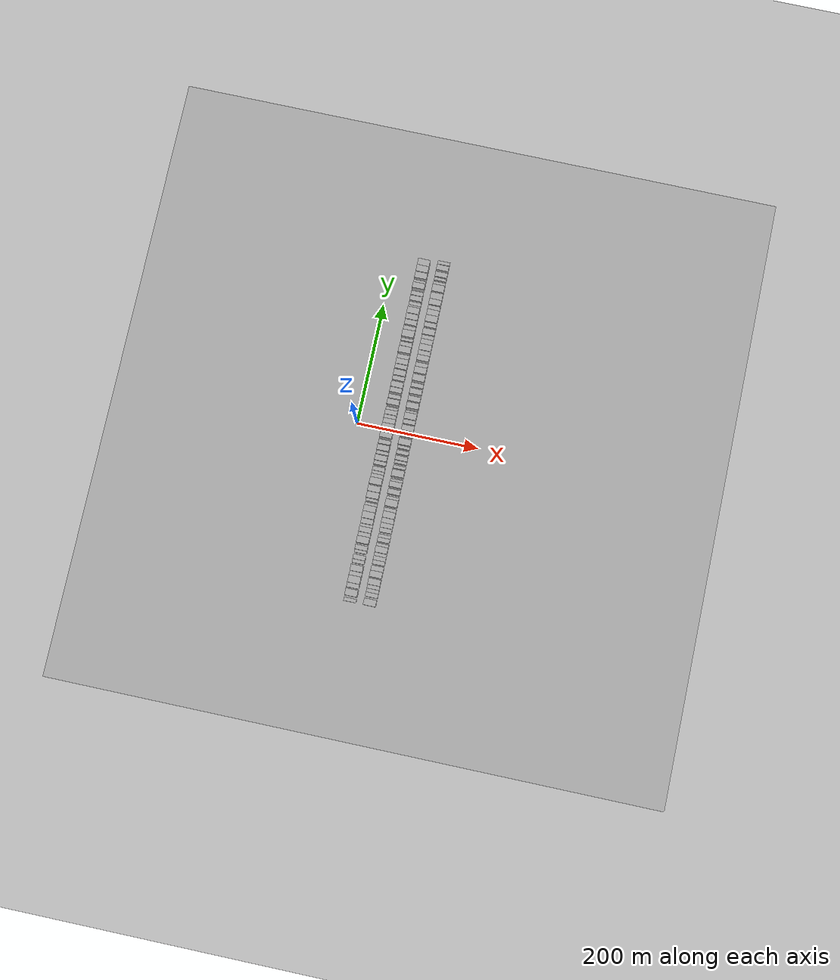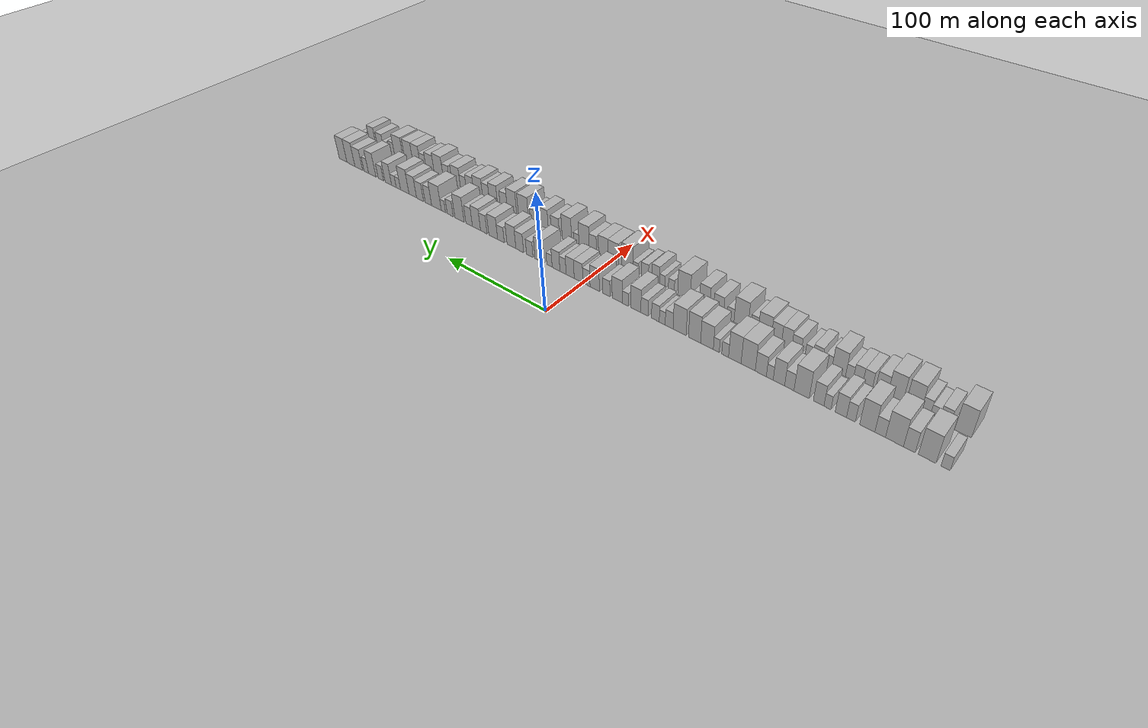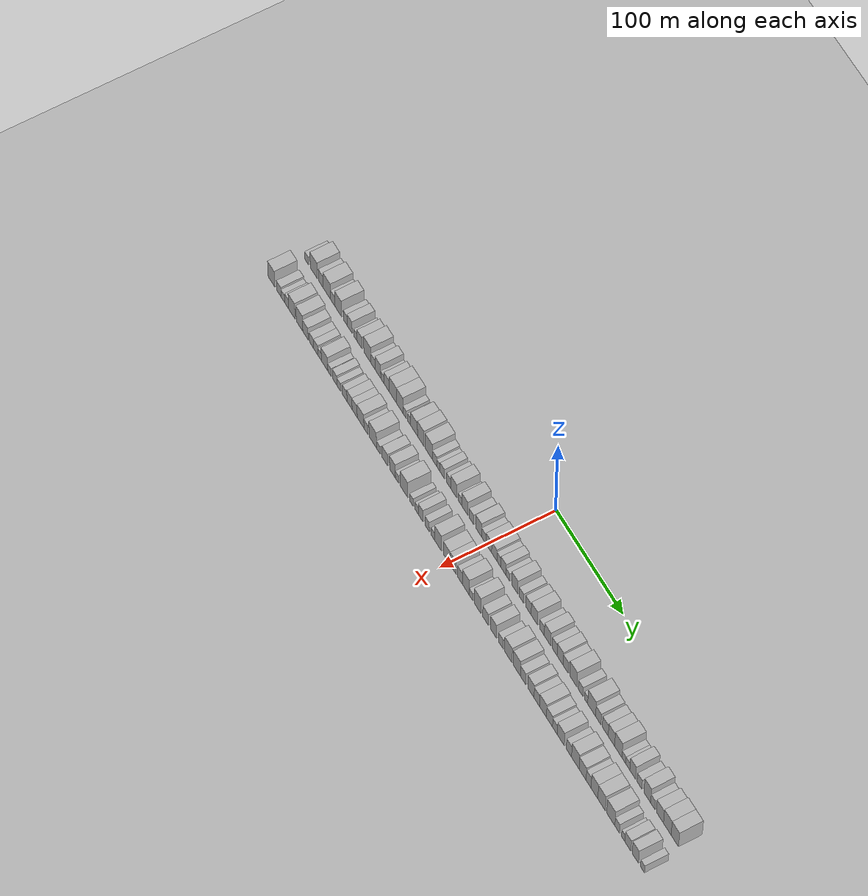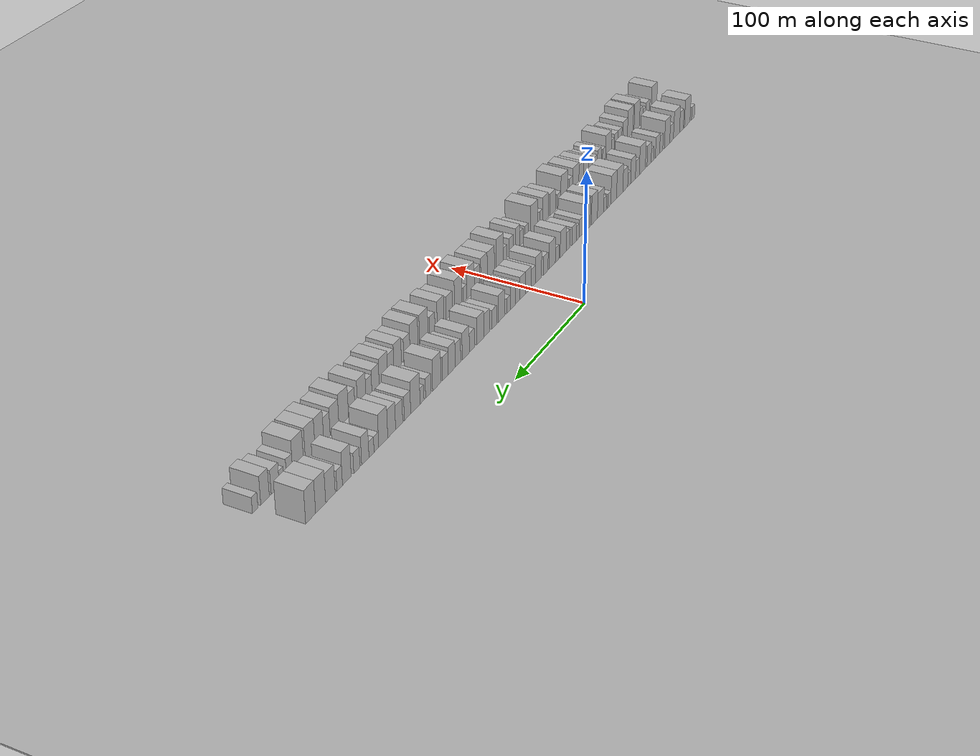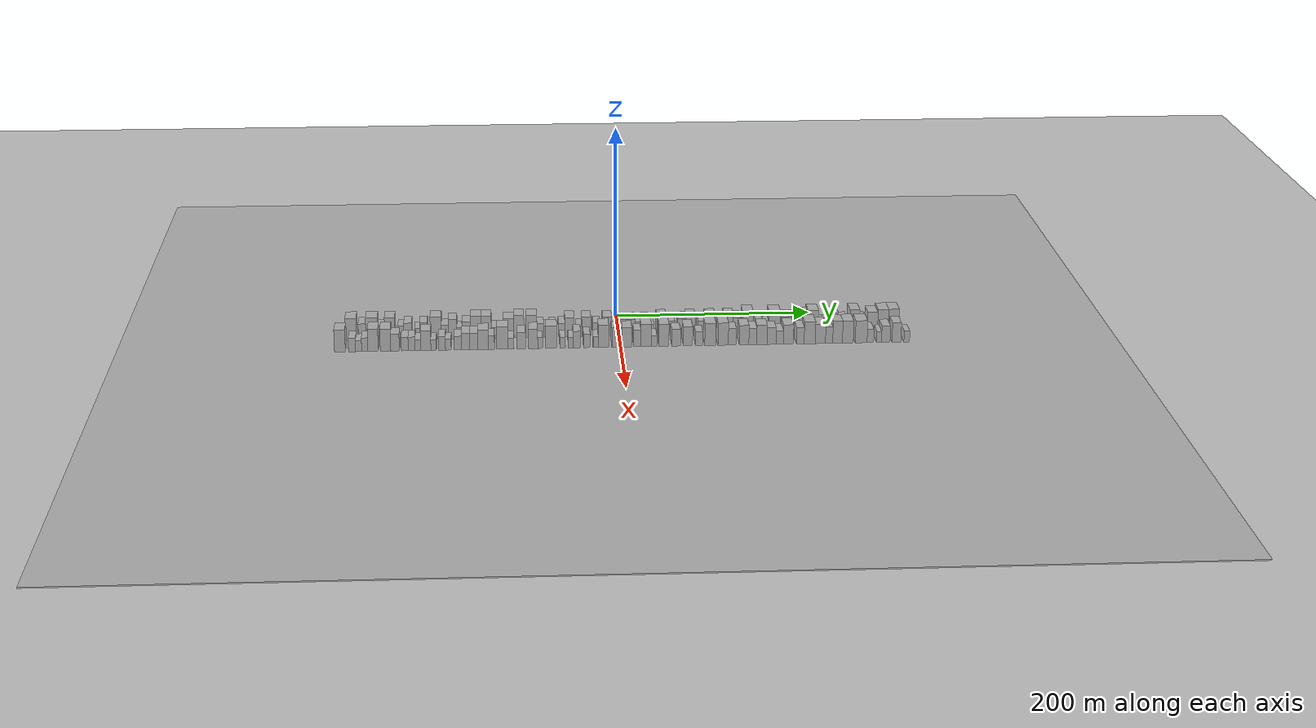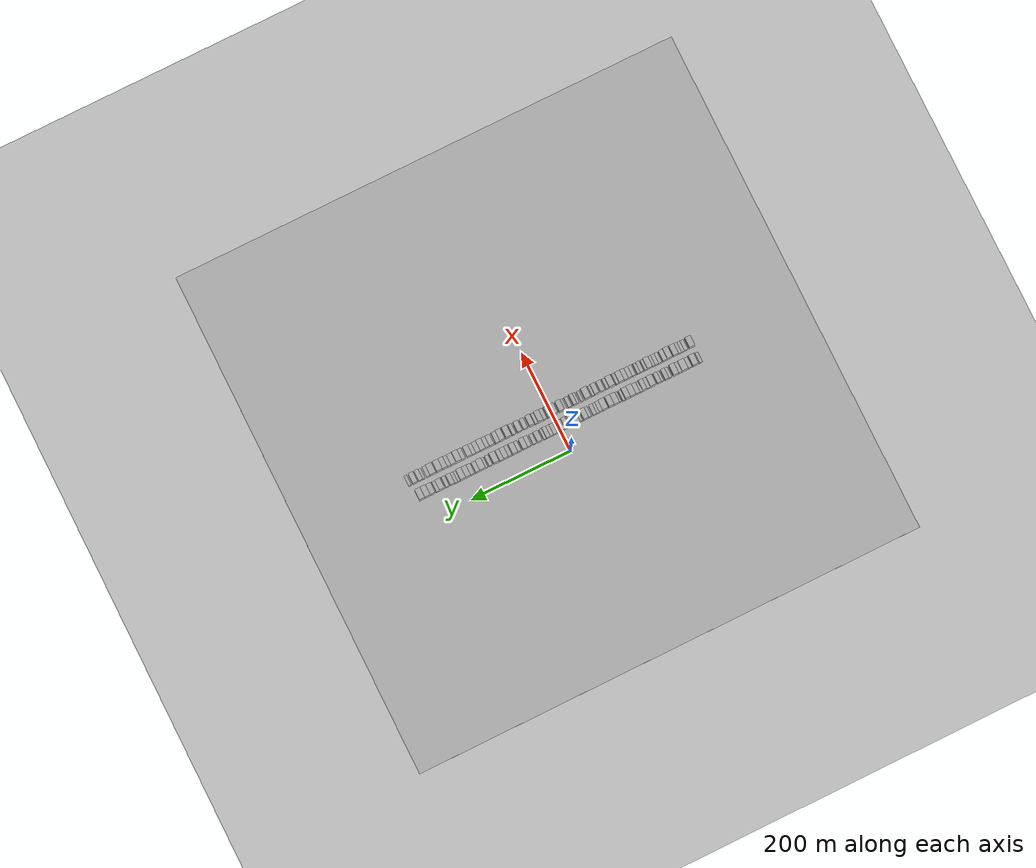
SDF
<?xml version="1.0" encoding="utf-8"?>

<sdf version="1.6">

   <world name="default">

      <gui fullscreen="0">

         <camera name="user_camera">

            <pose>-15 0 4.57585 0 0 0</pose>

            <view_controller>orbit</view_controller>

         </camera>

      </gui>

      <scene>

         <sky>

           <clouds>

             <speed>12</speed>

           </clouds>

         </sky>

         <ambient>0.4 0.4 0.4 1</ambient>

         <background>0.7 0.7 0.7 1</background>

         <shadows>1</shadows>

      </scene>

      <gravity>0 0 -9.8066</gravity>

      <magnetic_field>6e-06 2.3e-05 -4.2e-05</magnetic_field>

      <physics default="0" name="default_physics" type="ode">

         <ode>

            <solver>

               <type>quick</type>

               <iters>10</iters>

               <sor>1.0</sor>

               <use_dynamic_moi_rescaling>0</use_dynamic_moi_rescaling>

            </solver>

            <constraints>

               <cfm>0</cfm>

               <erp>0.2</erp>

               <contact_max_correcting_vel>100</contact_max_correcting_vel>

               <contact_surface_layer>0.001</contact_surface_layer>

            </constraints>

         </ode>

         <max_step_size>0.004</max_step_size>

         <real_time_factor>1</real_time_factor>

         <real_time_update_rate>250</real_time_update_rate>

      </physics>

      <light name="sun" type="directional">

         <cast_shadows>1</cast_shadows>

         <pose>0 0 10 0 0 0</pose>

         <diffuse>0.8 0.8 0.8 1</diffuse>

         <specular>0.2 0.2 0.2 1</specular>

         <attenuation>

            <range>1000</range>

            <constant>0.9</constant>

            <linear>0.01</linear>

            <quadratic>0.001</quadratic>

         </attenuation>

         <direction>-0.5 0.1 -0.9</direction>

      </light>

      <include>

         <name>ground_plane_1</name>

         <uri>model://HANNAS_ground_plane</uri>

         <pose>0 0 0  0 0 0</pose>

      </include>

      <include>

         <name>ground_plane_2</name>

         <uri>model://HANNAS_ground_plane</uri>

         <pose>100 0 0  0 0 0</pose>

      </include>

      <model name="building_1">

         <static>1</static>

         <pose frame="">50.0000 -281.1002 0 0.000000 0.000000 0.000000</pose>

         <link name="link">

            <pose frame="">0 0 6.00 0 0 0</pose>

            <collision name="collision">

               <geometry>

                  <box>

                     <size>20.0000 5.7995 12.0000</size>

                  </box>

               </geometry>

               <max_contacts>10</max_contacts>

               <surface>

                  <contact>

                     <ode/>

                  </contact>

                  <bounce/>

                  <friction>

                     <torsional>

                        <ode/>

                     </torsional>

                     <ode/>

                  </friction>

               </surface>

            </collision>

            <visual name="visual">

               <cast_shadows>0</cast_shadows>

               <geometry>

                  <box>

                     <size>20.0000 5.7995 12.0000</size>

                  </box>

               </geometry>

               <material>

                  <script>

                     <uri>model://HANNAS_wall/materials/scripts</uri>

                     <uri>model://HANNAS_wall/materials/textures</uri>

                     <name>vrc/HANNAS_wall</name>

                  </script>

               </material>

            </visual>

            <self_collide>0</self_collide>

            <enable_wind>0</enable_wind>

            <kinematic>0</kinematic>

         </link>

      </model>

      <model name="building_2">

         <static>1</static>

         <pose frame="">50.0000 -269.6048 0 0.000000 0.000000 0.000000</pose>

         <link name="link">

            <pose frame="">0 0 12.00 0 0 0</pose>

            <collision name="collision">

               <geometry>

                  <box>

                     <size>20.0000 11.1913 24.0000</size>

                  </box>

               </geometry>

               <max_contacts>10</max_contacts>

               <surface>

                  <contact>

                     <ode/>

                  </contact>

                  <bounce/>

                  <friction>

                     <torsional>

                        <ode/>

                     </torsional>

                     <ode/>

                  </friction>

               </surface>

            </collision>

            <visual name="visual">

               <cast_shadows>0</cast_shadows>

               <geometry>

                  <box>

                     <size>20.0000 11.1913 24.0000</size>

                  </box>

               </geometry>

               <material>

                  <script>

                     <uri>model://HANNAS_wall/materials/scripts</uri>

                     <uri>model://HANNAS_wall/materials/textures</uri>

                     <name>vrc/HANNAS_wall</name>

                  </script>

               </material>

            </visual>

            <self_collide>0</self_collide>

            <enable_wind>0</enable_wind>

            <kinematic>0</kinematic>

         </link>

      </model>

      <model name="building_3">

         <static>1</static>

         <pose frame="">50.0000 -258.2468 0 0.000000 0.000000 0.000000</pose>

         <link name="link">

            <pose frame="">0 0 9.00 0 0 0</pose>

            <collision name="collision">

               <geometry>

                  <box>

                     <size>20.0000 7.5247 18.0000</size>

                  </box>

               </geometry>

               <max_contacts>10</max_contacts>

               <surface>

                  <contact>

                     <ode/>

                  </contact>

                  <bounce/>

                  <friction>

                     <torsional>

                        <ode/>

                     </torsional>

                     <ode/>

                  </friction>

               </surface>

            </collision>

            <visual name="visual">

               <cast_shadows>0</cast_shadows>

               <geometry>

                  <box>

                     <size>20.0000 7.5247 18.0000</size>

                  </box>

               </geometry>

               <material>

                  <script>

                     <uri>model://HANNAS_wall/materials/scripts</uri>

                     <uri>model://HANNAS_wall/materials/textures</uri>

                     <name>vrc/HANNAS_wall</name>

                  </script>

               </material>

            </visual>

            <self_collide>0</self_collide>

            <enable_wind>0</enable_wind>

            <kinematic>0</kinematic>

         </link>

      </model>

      <model name="building_4">

         <static>1</static>

         <pose frame="">50.0000 -248.5909 0 0.000000 0.000000 0.000000</pose>

         <link name="link">

            <pose frame="">0 0 12.00 0 0 0</pose>

            <collision name="collision">

               <geometry>

                  <box>

                     <size>20.0000 11.7871 24.0000</size>

                  </box>

               </geometry>

               <max_contacts>10</max_contacts>

               <surface>

                  <contact>

                     <ode/>

                  </contact>

                  <bounce/>

                  <friction>

                     <torsional>

                        <ode/>

                     </torsional>

                     <ode/>

                  </friction>

               </surface>

            </collision>

            <visual name="visual">

               <cast_shadows>0</cast_shadows>

               <geometry>

                  <box>

                     <size>20.0000 11.7871 24.0000</size>

                  </box>

               </geometry>

               <material>

                  <script>

                     <uri>model://HANNAS_wall/materials/scripts</uri>

                     <uri>model://HANNAS_wall/materials/textures</uri>

                     <name>vrc/HANNAS_wall</name>

                  </script>

               </material>

            </visual>

            <self_collide>0</self_collide>

            <enable_wind>0</enable_wind>

            <kinematic>0</kinematic>

         </link>

      </model>

      <model name="building_5">

         <static>1</static>

         <pose frame="">50.0000 -239.1604 0 0.000000 0.000000 0.000000</pose>

         <link name="link">

            <pose frame="">0 0 7.50 0 0 0</pose>

            <collision name="collision">

               <geometry>

                  <box>

                     <size>20.0000 7.0738 15.0000</size>

                  </box>

               </geometry>

               <max_contacts>10</max_contacts>

               <surface>

                  <contact>

                     <ode/>

                  </contact>

                  <bounce/>

                  <friction>

                     <torsional>

                        <ode/>

                     </torsional>

                     <ode/>

                  </friction>

               </surface>

            </collision>

            <visual name="visual">

               <cast_shadows>0</cast_shadows>

               <geometry>

                  <box>

                     <size>20.0000 7.0738 15.0000</size>

                  </box>

               </geometry>

               <material>

                  <script>

                     <uri>model://HANNAS_wall/materials/scripts</uri>

                     <uri>model://HANNAS_wall/materials/textures</uri>

                     <name>vrc/HANNAS_wall</name>

                  </script>

               </material>

            </visual>

            <self_collide>0</self_collide>

            <enable_wind>0</enable_wind>

            <kinematic>0</kinematic>

         </link>

      </model>

      <model name="building_6">

         <static>1</static>

         <pose frame="">50.0000 -230.5154 0 0.000000 0.000000 0.000000</pose>

         <link name="link">

            <pose frame="">0 0 12.00 0 0 0</pose>

            <collision name="collision">

               <geometry>

                  <box>

                     <size>20.0000 10.2162 24.0000</size>

                  </box>

               </geometry>

               <max_contacts>10</max_contacts>

               <surface>

                  <contact>

                     <ode/>

                  </contact>

                  <bounce/>

                  <friction>

                     <torsional>

                        <ode/>

                     </torsional>

                     <ode/>

                  </friction>

               </surface>

            </collision>

            <visual name="visual">

               <cast_shadows>0</cast_shadows>

               <geometry>

                  <box>

                     <size>20.0000 10.2162 24.0000</size>

                  </box>

               </geometry>

               <material>

                  <script>

                     <uri>model://HANNAS_wall/materials/scripts</uri>

                     <uri>model://HANNAS_wall/materials/textures</uri>

                     <name>vrc/HANNAS_wall</name>

                  </script>

               </material>

            </visual>

            <self_collide>0</self_collide>

            <enable_wind>0</enable_wind>

            <kinematic>0</kinematic>

         </link>

      </model>

      <model name="building_7">

         <static>1</static>

         <pose frame="">50.0000 -219.3994 0 0.000000 0.000000 0.000000</pose>

         <link name="link">

            <pose frame="">0 0 7.50 0 0 0</pose>

            <collision name="collision">

               <geometry>

                  <box>

                     <size>20.0000 6.0159 15.0000</size>

                  </box>

               </geometry>

               <max_contacts>10</max_contacts>

               <surface>

                  <contact>

                     <ode/>

                  </contact>

                  <bounce/>

                  <friction>

                     <torsional>

                        <ode/>

                     </torsional>

                     <ode/>

                  </friction>

               </surface>

            </collision>

            <visual name="visual">

               <cast_shadows>0</cast_shadows>

               <geometry>

                  <box>

                     <size>20.0000 6.0159 15.0000</size>

                  </box>

               </geometry>

               <material>

                  <script>

                     <uri>model://HANNAS_wall/materials/scripts</uri>

                     <uri>model://HANNAS_wall/materials/textures</uri>

                     <name>vrc/HANNAS_wall</name>

                  </script>

               </material>

            </visual>

            <self_collide>0</self_collide>

            <enable_wind>0</enable_wind>

            <kinematic>0</kinematic>

         </link>

      </model>

      <model name="building_8">

         <static>1</static>

         <pose frame="">50.0000 -212.4667 0 0.000000 0.000000 0.000000</pose>

         <link name="link">

            <pose frame="">0 0 9.00 0 0 0</pose>

            <collision name="collision">

               <geometry>

                  <box>

                     <size>20.0000 7.8495 18.0000</size>

                  </box>

               </geometry>

               <max_contacts>10</max_contacts>

               <surface>

                  <contact>

                     <ode/>

                  </contact>

                  <bounce/>

                  <friction>

                     <torsional>

                        <ode/>

                     </torsional>

                     <ode/>

                  </friction>

               </surface>

            </collision>

            <visual name="visual">

               <cast_shadows>0</cast_shadows>

               <geometry>

                  <box>

                     <size>20.0000 7.8495 18.0000</size>

                  </box>

               </geometry>

               <material>

                  <script>

                     <uri>model://HANNAS_wall/materials/scripts</uri>

                     <uri>model://HANNAS_wall/materials/textures</uri>

                     <name>vrc/HANNAS_wall</name>

                  </script>

               </material>

            </visual>

            <self_collide>0</self_collide>

            <enable_wind>0</enable_wind>

            <kinematic>0</kinematic>

         </link>

      </model>

      <model name="building_9">

         <static>1</static>

         <pose frame="">50.0000 -203.0691 0 0.000000 0.000000 0.000000</pose>

         <link name="link">

            <pose frame="">0 0 6.00 0 0 0</pose>

            <collision name="collision">

               <geometry>

                  <box>

                     <size>20.0000 4.9457 12.0000</size>

                  </box>

               </geometry>

               <max_contacts>10</max_contacts>

               <surface>

                  <contact>

                     <ode/>

                  </contact>

                  <bounce/>

                  <friction>

                     <torsional>

                        <ode/>

                     </torsional>

                     <ode/>

                  </friction>

               </surface>

            </collision>

            <visual name="visual">

               <cast_shadows>0</cast_shadows>

               <geometry>

                  <box>

                     <size>20.0000 4.9457 12.0000</size>

                  </box>

               </geometry>

               <material>

                  <script>

                     <uri>model://HANNAS_wall/materials/scripts</uri>

                     <uri>model://HANNAS_wall/materials/textures</uri>

                     <name>vrc/HANNAS_wall</name>

                  </script>

               </material>

            </visual>

            <self_collide>0</self_collide>

            <enable_wind>0</enable_wind>

            <kinematic>0</kinematic>

         </link>

      </model>

      <model name="building_10">

         <static>1</static>

         <pose frame="">50.0000 -196.8094 0 0.000000 0.000000 0.000000</pose>

         <link name="link">

            <pose frame="">0 0 9.00 0 0 0</pose>

            <collision name="collision">

               <geometry>

                  <box>

                     <size>20.0000 7.5737 18.0000</size>

                  </box>

               </geometry>

               <max_contacts>10</max_contacts>

               <surface>

                  <contact>

                     <ode/>

                  </contact>

                  <bounce/>

                  <friction>

                     <torsional>

                        <ode/>

                     </torsional>

                     <ode/>

                  </friction>

               </surface>

            </collision>

            <visual name="visual">

               <cast_shadows>0</cast_shadows>

               <geometry>

                  <box>

                     <size>20.0000 7.5737 18.0000</size>

                  </box>

               </geometry>

               <material>

                  <script>

                     <uri>model://HANNAS_wall/materials/scripts</uri>

                     <uri>model://HANNAS_wall/materials/textures</uri>

                     <name>vrc/HANNAS_wall</name>

                  </script>

               </material>

            </visual>

            <self_collide>0</self_collide>

            <enable_wind>0</enable_wind>

            <kinematic>0</kinematic>

         </link>

      </model>

      <model name="building_11">

         <static>1</static>

         <pose frame="">50.0000 -184.4767 0 0.000000 0.000000 0.000000</pose>

         <link name="link">

            <pose frame="">0 0 12.00 0 0 0</pose>

            <collision name="collision">

               <geometry>

                  <box>

                     <size>20.0000 11.0915 24.0000</size>

                  </box>

               </geometry>

               <max_contacts>10</max_contacts>

               <surface>

                  <contact>

                     <ode/>

                  </contact>

                  <bounce/>

                  <friction>

                     <torsional>

                        <ode/>

                     </torsional>

                     <ode/>

                  </friction>

               </surface>

            </collision>

            <visual name="visual">

               <cast_shadows>0</cast_shadows>

               <geometry>

                  <box>

                     <size>20.0000 11.0915 24.0000</size>

                  </box>

               </geometry>

               <material>

                  <script>

                     <uri>model://HANNAS_wall/materials/scripts</uri>

                     <uri>model://HANNAS_wall/materials/textures</uri>

                     <name>vrc/HANNAS_wall</name>

                  </script>

               </material>

            </visual>

            <self_collide>0</self_collide>

            <enable_wind>0</enable_wind>

            <kinematic>0</kinematic>

         </link>

      </model>

      <model name="building_12">

         <static>1</static>

         <pose frame="">50.0000 -175.4597 0 0.000000 0.000000 0.000000</pose>

         <link name="link">

            <pose frame="">0 0 7.50 0 0 0</pose>

            <collision name="collision">

               <geometry>

                  <box>

                     <size>20.0000 6.9426 15.0000</size>

                  </box>

               </geometry>

               <max_contacts>10</max_contacts>

               <surface>

                  <contact>

                     <ode/>

                  </contact>

                  <bounce/>

                  <friction>

                     <torsional>

                        <ode/>

                     </torsional>

                     <ode/>

                  </friction>

               </surface>

            </collision>

            <visual name="visual">

               <cast_shadows>0</cast_shadows>

               <geometry>

                  <box>

                     <size>20.0000 6.9426 15.0000</size>

                  </box>

               </geometry>

               <material>

                  <script>

                     <uri>model://HANNAS_wall/materials/scripts</uri>

                     <uri>model://HANNAS_wall/materials/textures</uri>

                     <name>vrc/HANNAS_wall</name>

                  </script>

               </material>

            </visual>

            <self_collide>0</self_collide>

            <enable_wind>0</enable_wind>

            <kinematic>0</kinematic>

         </link>

      </model>

      <model name="building_13">

         <static>1</static>

         <pose frame="">50.0000 -167.6917 0 0.000000 0.000000 0.000000</pose>

         <link name="link">

            <pose frame="">0 0 10.50 0 0 0</pose>

            <collision name="collision">

               <geometry>

                  <box>

                     <size>20.0000 8.5933 21.0000</size>

                  </box>

               </geometry>

               <max_contacts>10</max_contacts>

               <surface>

                  <contact>

                     <ode/>

                  </contact>

                  <bounce/>

                  <friction>

                     <torsional>

                        <ode/>

                     </torsional>

                     <ode/>

                  </friction>

               </surface>

            </collision>

            <visual name="visual">

               <cast_shadows>0</cast_shadows>

               <geometry>

                  <box>

                     <size>20.0000 8.5933 21.0000</size>

                  </box>

               </geometry>

               <material>

                  <script>

                     <uri>model://HANNAS_wall/materials/scripts</uri>

                     <uri>model://HANNAS_wall/materials/textures</uri>

                     <name>vrc/HANNAS_wall</name>

                  </script>

               </material>

            </visual>

            <self_collide>0</self_collide>

            <enable_wind>0</enable_wind>

            <kinematic>0</kinematic>

         </link>

      </model>

      <model name="building_14">

         <static>1</static>

         <pose frame="">50.0000 -160.8005 0 0.000000 0.000000 0.000000</pose>

         <link name="link">

            <pose frame="">0 0 6.00 0 0 0</pose>

            <collision name="collision">

               <geometry>

                  <box>

                     <size>20.0000 5.1891 12.0000</size>

                  </box>

               </geometry>

               <max_contacts>10</max_contacts>

               <surface>

                  <contact>

                     <ode/>

                  </contact>

                  <bounce/>

                  <friction>

                     <torsional>

                        <ode/>

                     </torsional>

                     <ode/>

                  </friction>

               </surface>

            </collision>

            <visual name="visual">

               <cast_shadows>0</cast_shadows>

               <geometry>

                  <box>

                     <size>20.0000 5.1891 12.0000</size>

                  </box>

               </geometry>

               <material>

                  <script>

                     <uri>model://HANNAS_wall/materials/scripts</uri>

                     <uri>model://HANNAS_wall/materials/textures</uri>

                     <name>vrc/HANNAS_wall</name>

                  </script>

               </material>

            </visual>

            <self_collide>0</self_collide>

            <enable_wind>0</enable_wind>

            <kinematic>0</kinematic>

         </link>

      </model>

      <model name="building_15">

         <static>1</static>

         <pose frame="">50.0000 -153.9684 0 0.000000 0.000000 0.000000</pose>

         <link name="link">

            <pose frame="">0 0 9.00 0 0 0</pose>

            <collision name="collision">

               <geometry>

                  <box>

                     <size>20.0000 8.4751 18.0000</size>

                  </box>

               </geometry>

               <max_contacts>10</max_contacts>

               <surface>

                  <contact>

                     <ode/>

                  </contact>

                  <bounce/>

                  <friction>

                     <torsional>

                        <ode/>

                     </torsional>

                     <ode/>

                  </friction>

               </surface>

            </collision>

            <visual name="visual">

               <cast_shadows>0</cast_shadows>

               <geometry>

                  <box>

                     <size>20.0000 8.4751 18.0000</size>

                  </box>

               </geometry>

               <material>

                  <script>

                     <uri>model://HANNAS_wall/materials/scripts</uri>

                     <uri>model://HANNAS_wall/materials/textures</uri>

                     <name>vrc/HANNAS_wall</name>

                  </script>

               </material>

            </visual>

            <self_collide>0</self_collide>

            <enable_wind>0</enable_wind>

            <kinematic>0</kinematic>

         </link>

      </model>

      <model name="building_16">

         <static>1</static>

         <pose frame="">50.0000 -144.1960 0 0.000000 0.000000 0.000000</pose>

         <link name="link">

            <pose frame="">0 0 12.00 0 0 0</pose>

            <collision name="collision">

               <geometry>

                  <box>

                     <size>20.0000 11.0698 24.0000</size>

                  </box>

               </geometry>

               <max_contacts>10</max_contacts>

               <surface>

                  <contact>

                     <ode/>

                  </contact>

                  <bounce/>

                  <friction>

                     <torsional>

                        <ode/>

                     </torsional>

                     <ode/>

                  </friction>

               </surface>

            </collision>

            <visual name="visual">

               <cast_shadows>0</cast_shadows>

               <geometry>

                  <box>

                     <size>20.0000 11.0698 24.0000</size>

                  </box>

               </geometry>

               <material>

                  <script>

                     <uri>model://HANNAS_wall/materials/scripts</uri>

                     <uri>model://HANNAS_wall/materials/textures</uri>

                     <name>vrc/HANNAS_wall</name>

                  </script>

               </material>

            </visual>

            <self_collide>0</self_collide>

            <enable_wind>0</enable_wind>

            <kinematic>0</kinematic>

         </link>

      </model>

      <model name="building_17">

         <static>1</static>

         <pose frame="">50.0000 -133.6998 0 0.000000 0.000000 0.000000</pose>

         <link name="link">

            <pose frame="">0 0 12.00 0 0 0</pose>

            <collision name="collision">

               <geometry>

                  <box>

                     <size>20.0000 9.9225 24.0000</size>

                  </box>

               </geometry>

               <max_contacts>10</max_contacts>

               <surface>

                  <contact>

                     <ode/>

                  </contact>

                  <bounce/>

                  <friction>

                     <torsional>

                        <ode/>

                     </torsional>

                     <ode/>

                  </friction>

               </surface>

            </collision>

            <visual name="visual">

               <cast_shadows>0</cast_shadows>

               <geometry>

                  <box>

                     <size>20.0000 9.9225 24.0000</size>

                  </box>

               </geometry>

               <material>

                  <script>

                     <uri>model://HANNAS_wall/materials/scripts</uri>

                     <uri>model://HANNAS_wall/materials/textures</uri>

                     <name>vrc/HANNAS_wall</name>

                  </script>

               </material>

            </visual>

            <self_collide>0</self_collide>

            <enable_wind>0</enable_wind>

            <kinematic>0</kinematic>

         </link>

      </model>

      <model name="building_18">

         <static>1</static>

         <pose frame="">50.0000 -126.0071 0 0.000000 0.000000 0.000000</pose>

         <link name="link">

            <pose frame="">0 0 6.00 0 0 0</pose>

            <collision name="collision">

               <geometry>

                  <box>

                     <size>20.0000 5.4629 12.0000</size>

                  </box>

               </geometry>

               <max_contacts>10</max_contacts>

               <surface>

                  <contact>

                     <ode/>

                  </contact>

                  <bounce/>

                  <friction>

                     <torsional>

                        <ode/>

                     </torsional>

                     <ode/>

                  </friction>

               </surface>

            </collision>

            <visual name="visual">

               <cast_shadows>0</cast_shadows>

               <geometry>

                  <box>

                     <size>20.0000 5.4629 12.0000</size>

                  </box>

               </geometry>

               <material>

                  <script>

                     <uri>model://HANNAS_wall/materials/scripts</uri>

                     <uri>model://HANNAS_wall/materials/textures</uri>

                     <name>vrc/HANNAS_wall</name>

                  </script>

               </material>

            </visual>

            <self_collide>0</self_collide>

            <enable_wind>0</enable_wind>

            <kinematic>0</kinematic>

         </link>

      </model>

      <model name="building_19">

         <static>1</static>

         <pose frame="">50.0000 -118.8650 0 0.000000 0.000000 0.000000</pose>

         <link name="link">

            <pose frame="">0 0 6.00 0 0 0</pose>

            <collision name="collision">

               <geometry>

                  <box>

                     <size>20.0000 4.8213 12.0000</size>

                  </box>

               </geometry>

               <max_contacts>10</max_contacts>

               <surface>

                  <contact>

                     <ode/>

                  </contact>

                  <bounce/>

                  <friction>

                     <torsional>

                        <ode/>

                     </torsional>

                     <ode/>

                  </friction>

               </surface>

            </collision>

            <visual name="visual">

               <cast_shadows>0</cast_shadows>

               <geometry>

                  <box>

                     <size>20.0000 4.8213 12.0000</size>

                  </box>

               </geometry>

               <material>

                  <script>

                     <uri>model://HANNAS_wall/materials/scripts</uri>

                     <uri>model://HANNAS_wall/materials/textures</uri>

                     <name>vrc/HANNAS_wall</name>

                  </script>

               </material>

            </visual>

            <self_collide>0</self_collide>

            <enable_wind>0</enable_wind>

            <kinematic>0</kinematic>

         </link>

      </model>

      <model name="building_20">

         <static>1</static>

         <pose frame="">50.0000 -111.2466 0 0.000000 0.000000 0.000000</pose>

         <link name="link">

            <pose frame="">0 0 10.50 0 0 0</pose>

            <collision name="collision">

               <geometry>

                  <box>

                     <size>20.0000 10.4155 21.0000</size>

                  </box>

               </geometry>

               <max_contacts>10</max_contacts>

               <surface>

                  <contact>

                     <ode/>

                  </contact>

                  <bounce/>

                  <friction>

                     <torsional>

                        <ode/>

                     </torsional>

                     <ode/>

                  </friction>

               </surface>

            </collision>

            <visual name="visual">

               <cast_shadows>0</cast_shadows>

               <geometry>

                  <box>

                     <size>20.0000 10.4155 21.0000</size>

                  </box>

               </geometry>

               <material>

                  <script>

                     <uri>model://HANNAS_wall/materials/scripts</uri>

                     <uri>model://HANNAS_wall/materials/textures</uri>

                     <name>vrc/HANNAS_wall</name>

                  </script>

               </material>

            </visual>

            <self_collide>0</self_collide>

            <enable_wind>0</enable_wind>

            <kinematic>0</kinematic>

         </link>

      </model>

      <model name="building_21">

         <static>1</static>

         <pose frame="">50.0000 -100.9907 0 0.000000 0.000000 0.000000</pose>

         <link name="link">

            <pose frame="">0 0 12.00 0 0 0</pose>

            <collision name="collision">

               <geometry>

                  <box>

                     <size>20.0000 10.0962 24.0000</size>

                  </box>

               </geometry>

               <max_contacts>10</max_contacts>

               <surface>

                  <contact>

                     <ode/>

                  </contact>

                  <bounce/>

                  <friction>

                     <torsional>

                        <ode/>

                     </torsional>

                     <ode/>

                  </friction>

               </surface>

            </collision>

            <visual name="visual">

               <cast_shadows>0</cast_shadows>

               <geometry>

                  <box>

                     <size>20.0000 10.0962 24.0000</size>

                  </box>

               </geometry>

               <material>

                  <script>

                     <uri>model://HANNAS_wall/materials/scripts</uri>

                     <uri>model://HANNAS_wall/materials/textures</uri>

                     <name>vrc/HANNAS_wall</name>

                  </script>

               </material>

            </visual>

            <self_collide>0</self_collide>

            <enable_wind>0</enable_wind>

            <kinematic>0</kinematic>

         </link>

      </model>

      <model name="building_22">

         <static>1</static>

         <pose frame="">50.0000 -88.4051 0 0.000000 0.000000 0.000000</pose>

         <link name="link">

            <pose frame="">0 0 12.00 0 0 0</pose>

            <collision name="collision">

               <geometry>

                  <box>

                     <size>20.0000 11.0750 24.0000</size>

                  </box>

               </geometry>

               <max_contacts>10</max_contacts>

               <surface>

                  <contact>

                     <ode/>

                  </contact>

                  <bounce/>

                  <friction>

                     <torsional>

                        <ode/>

                     </torsional>

                     <ode/>

                  </friction>

               </surface>

            </collision>

            <visual name="visual">

               <cast_shadows>0</cast_shadows>

               <geometry>

                  <box>

                     <size>20.0000 11.0750 24.0000</size>

                  </box>

               </geometry>

               <material>

                  <script>

                     <uri>model://HANNAS_wall/materials/scripts</uri>

                     <uri>model://HANNAS_wall/materials/textures</uri>

                     <name>vrc/HANNAS_wall</name>

                  </script>

               </material>

            </visual>

            <self_collide>0</self_collide>

            <enable_wind>0</enable_wind>

            <kinematic>0</kinematic>

         </link>

      </model>

      <model name="building_23">

         <static>1</static>

         <pose frame="">50.0000 -79.4754 0 0.000000 0.000000 0.000000</pose>

         <link name="link">

            <pose frame="">0 0 7.50 0 0 0</pose>

            <collision name="collision">

               <geometry>

                  <box>

                     <size>20.0000 6.7845 15.0000</size>

                  </box>

               </geometry>

               <max_contacts>10</max_contacts>

               <surface>

                  <contact>

                     <ode/>

                  </contact>

                  <bounce/>

                  <friction>

                     <torsional>

                        <ode/>

                     </torsional>

                     <ode/>

                  </friction>

               </surface>

            </collision>

            <visual name="visual">

               <cast_shadows>0</cast_shadows>

               <geometry>

                  <box>

                     <size>20.0000 6.7845 15.0000</size>

                  </box>

               </geometry>

               <material>

                  <script>

                     <uri>model://HANNAS_wall/materials/scripts</uri>

                     <uri>model://HANNAS_wall/materials/textures</uri>

                     <name>vrc/HANNAS_wall</name>

                  </script>

               </material>

            </visual>

            <self_collide>0</self_collide>

            <enable_wind>0</enable_wind>

            <kinematic>0</kinematic>

         </link>

      </model>

      <model name="building_24">

         <static>1</static>

         <pose frame="">50.0000 -73.4799 0 0.000000 0.000000 0.000000</pose>

         <link name="link">

            <pose frame="">0 0 6.00 0 0 0</pose>

            <collision name="collision">

               <geometry>

                  <box>

                     <size>20.0000 5.2065 12.0000</size>

                  </box>

               </geometry>

               <max_contacts>10</max_contacts>

               <surface>

                  <contact>

                     <ode/>

                  </contact>

                  <bounce/>

                  <friction>

                     <torsional>

                        <ode/>

                     </torsional>

                     <ode/>

                  </friction>

               </surface>

            </collision>

            <visual name="visual">

               <cast_shadows>0</cast_shadows>

               <geometry>

                  <box>

                     <size>20.0000 5.2065 12.0000</size>

                  </box>

               </geometry>

               <material>

                  <script>

                     <uri>model://HANNAS_wall/materials/scripts</uri>

                     <uri>model://HANNAS_wall/materials/textures</uri>

                     <name>vrc/HANNAS_wall</name>

                  </script>

               </material>

            </visual>

            <self_collide>0</self_collide>

            <enable_wind>0</enable_wind>

            <kinematic>0</kinematic>

         </link>

      </model>

      <model name="building_25">

         <static>1</static>

         <pose frame="">50.0000 -67.5074 0 0.000000 0.000000 0.000000</pose>

         <link name="link">

            <pose frame="">0 0 7.50 0 0 0</pose>

            <collision name="collision">

               <geometry>

                  <box>

                     <size>20.0000 6.7385 15.0000</size>

                  </box>

               </geometry>

               <max_contacts>10</max_contacts>

               <surface>

                  <contact>

                     <ode/>

                  </contact>

                  <bounce/>

                  <friction>

                     <torsional>

                        <ode/>

                     </torsional>

                     <ode/>

                  </friction>

               </surface>

            </collision>

            <visual name="visual">

               <cast_shadows>0</cast_shadows>

               <geometry>

                  <box>

                     <size>20.0000 6.7385 15.0000</size>

                  </box>

               </geometry>

               <material>

                  <script>

                     <uri>model://HANNAS_wall/materials/scripts</uri>

                     <uri>model://HANNAS_wall/materials/textures</uri>

                     <name>vrc/HANNAS_wall</name>

                  </script>

               </material>

            </visual>

            <self_collide>0</self_collide>

            <enable_wind>0</enable_wind>

            <kinematic>0</kinematic>

         </link>

      </model>

      <model name="building_26">

         <static>1</static>

         <pose frame="">50.0000 -57.9240 0 0.000000 0.000000 0.000000</pose>

         <link name="link">

            <pose frame="">0 0 7.50 0 0 0</pose>

            <collision name="collision">

               <geometry>

                  <box>

                     <size>20.0000 6.4283 15.0000</size>

                  </box>

               </geometry>

               <max_contacts>10</max_contacts>

               <surface>

                  <contact>

                     <ode/>

                  </contact>

                  <bounce/>

                  <friction>

                     <torsional>

                        <ode/>

                     </torsional>

                     <ode/>

                  </friction>

               </surface>

            </collision>

            <visual name="visual">

               <cast_shadows>0</cast_shadows>

               <geometry>

                  <box>

                     <size>20.0000 6.4283 15.0000</size>

                  </box>

               </geometry>

               <material>

                  <script>

                     <uri>model://HANNAS_wall/materials/scripts</uri>

                     <uri>model://HANNAS_wall/materials/textures</uri>

                     <name>vrc/HANNAS_wall</name>

                  </script>

               </material>

            </visual>

            <self_collide>0</self_collide>

            <enable_wind>0</enable_wind>

            <kinematic>0</kinematic>

         </link>

      </model>

      <model name="building_27">

         <static>1</static>

         <pose frame="">50.0000 -50.0287 0 0.000000 0.000000 0.000000</pose>

         <link name="link">

            <pose frame="">0 0 10.50 0 0 0</pose>

            <collision name="collision">

               <geometry>

                  <box>

                     <size>20.0000 9.3624 21.0000</size>

                  </box>

               </geometry>

               <max_contacts>10</max_contacts>

               <surface>

                  <contact>

                     <ode/>

                  </contact>

                  <bounce/>

                  <friction>

                     <torsional>

                        <ode/>

                     </torsional>

                     <ode/>

                  </friction>

               </surface>

            </collision>

            <visual name="visual">

               <cast_shadows>0</cast_shadows>

               <geometry>

                  <box>

                     <size>20.0000 9.3624 21.0000</size>

                  </box>

               </geometry>

               <material>

                  <script>

                     <uri>model://HANNAS_wall/materials/scripts</uri>

                     <uri>model://HANNAS_wall/materials/textures</uri>

                     <name>vrc/HANNAS_wall</name>

                  </script>

               </material>

            </visual>

            <self_collide>0</self_collide>

            <enable_wind>0</enable_wind>

            <kinematic>0</kinematic>

         </link>

      </model>

      <model name="building_28">

         <static>1</static>

         <pose frame="">50.0000 -40.5329 0 0.000000 0.000000 0.000000</pose>

         <link name="link">

            <pose frame="">0 0 6.00 0 0 0</pose>

            <collision name="collision">

               <geometry>

                  <box>

                     <size>20.0000 5.6292 12.0000</size>

                  </box>

               </geometry>

               <max_contacts>10</max_contacts>

               <surface>

                  <contact>

                     <ode/>

                  </contact>

                  <bounce/>

                  <friction>

                     <torsional>

                        <ode/>

                     </torsional>

                     <ode/>

                  </friction>

               </surface>

            </collision>

            <visual name="visual">

               <cast_shadows>0</cast_shadows>

               <geometry>

                  <box>

                     <size>20.0000 5.6292 12.0000</size>

                  </box>

               </geometry>

               <material>

                  <script>

                     <uri>model://HANNAS_wall/materials/scripts</uri>

                     <uri>model://HANNAS_wall/materials/textures</uri>

                     <name>vrc/HANNAS_wall</name>

                  </script>

               </material>

            </visual>

            <self_collide>0</self_collide>

            <enable_wind>0</enable_wind>

            <kinematic>0</kinematic>

         </link>

      </model>

      <model name="building_29">

         <static>1</static>

         <pose frame="">50.0000 -33.0718 0 0.000000 0.000000 0.000000</pose>

         <link name="link">

            <pose frame="">0 0 10.50 0 0 0</pose>

            <collision name="collision">

               <geometry>

                  <box>

                     <size>20.0000 9.2932 21.0000</size>

                  </box>

               </geometry>

               <max_contacts>10</max_contacts>

               <surface>

                  <contact>

                     <ode/>

                  </contact>

                  <bounce/>

                  <friction>

                     <torsional>

                        <ode/>

                     </torsional>

                     <ode/>

                  </friction>

               </surface>

            </collision>

            <visual name="visual">

               <cast_shadows>0</cast_shadows>

               <geometry>

                  <box>

                     <size>20.0000 9.2932 21.0000</size>

                  </box>

               </geometry>

               <material>

                  <script>

                     <uri>model://HANNAS_wall/materials/scripts</uri>

                     <uri>model://HANNAS_wall/materials/textures</uri>

                     <name>vrc/HANNAS_wall</name>

                  </script>

               </material>

            </visual>

            <self_collide>0</self_collide>

            <enable_wind>0</enable_wind>

            <kinematic>0</kinematic>

         </link>

      </model>

      <model name="building_30">

         <static>1</static>

         <pose frame="">50.0000 -22.9545 0 0.000000 0.000000 0.000000</pose>

         <link name="link">

            <pose frame="">0 0 7.50 0 0 0</pose>

            <collision name="collision">

               <geometry>

                  <box>

                     <size>20.0000 6.9413 15.0000</size>

                  </box>

               </geometry>

               <max_contacts>10</max_contacts>

               <surface>

                  <contact>

                     <ode/>

                  </contact>

                  <bounce/>

                  <friction>

                     <torsional>

                        <ode/>

                     </torsional>

                     <ode/>

                  </friction>

               </surface>

            </collision>

            <visual name="visual">

               <cast_shadows>0</cast_shadows>

               <geometry>

                  <box>

                     <size>20.0000 6.9413 15.0000</size>

                  </box>

               </geometry>

               <material>

                  <script>

                     <uri>model://HANNAS_wall/materials/scripts</uri>

                     <uri>model://HANNAS_wall/materials/textures</uri>

                     <name>vrc/HANNAS_wall</name>

                  </script>

               </material>

            </visual>

            <self_collide>0</self_collide>

            <enable_wind>0</enable_wind>

            <kinematic>0</kinematic>

         </link>

      </model>

      <model name="building_31">

         <static>1</static>

         <pose frame="">50.0000 -11.9963 0 0.000000 0.000000 0.000000</pose>

         <link name="link">

            <pose frame="">0 0 10.50 0 0 0</pose>

            <collision name="collision">

               <geometry>

                  <box>

                     <size>20.0000 8.9750 21.0000</size>

                  </box>

               </geometry>

               <max_contacts>10</max_contacts>

               <surface>

                  <contact>

                     <ode/>

                  </contact>

                  <bounce/>

                  <friction>

                     <torsional>

                        <ode/>

                     </torsional>

                     <ode/>

                  </friction>

               </surface>

            </collision>

            <visual name="visual">

               <cast_shadows>0</cast_shadows>

               <geometry>

                  <box>

                     <size>20.0000 8.9750 21.0000</size>

                  </box>

               </geometry>

               <material>

                  <script>

                     <uri>model://HANNAS_wall/materials/scripts</uri>

                     <uri>model://HANNAS_wall/materials/textures</uri>

                     <name>vrc/HANNAS_wall</name>

                  </script>

               </material>

            </visual>

            <self_collide>0</self_collide>

            <enable_wind>0</enable_wind>

            <kinematic>0</kinematic>

         </link>

      </model>

      <model name="building_32">

         <static>1</static>

         <pose frame="">50.0000 -4.1049 0 0.000000 0.000000 0.000000</pose>

         <link name="link">

            <pose frame="">0 0 7.50 0 0 0</pose>

            <collision name="collision">

               <geometry>

                  <box>

                     <size>20.0000 6.8079 15.0000</size>

                  </box>

               </geometry>

               <max_contacts>10</max_contacts>

               <surface>

                  <contact>

                     <ode/>

                  </contact>

                  <bounce/>

                  <friction>

                     <torsional>

                        <ode/>

                     </torsional>

                     <ode/>

                  </friction>

               </surface>

            </collision>

            <visual name="visual">

               <cast_shadows>0</cast_shadows>

               <geometry>

                  <box>

                     <size>20.0000 6.8079 15.0000</size>

                  </box>

               </geometry>

               <material>

                  <script>

                     <uri>model://HANNAS_wall/materials/scripts</uri>

                     <uri>model://HANNAS_wall/materials/textures</uri>

                     <name>vrc/HANNAS_wall</name>

                  </script>

               </material>

            </visual>

            <self_collide>0</self_collide>

            <enable_wind>0</enable_wind>

            <kinematic>0</kinematic>

         </link>

      </model>

      <model name="building_33">

         <static>1</static>

         <pose frame="">50.0000 3.5767 0 0.000000 0.000000 0.000000</pose>

         <link name="link">

            <pose frame="">0 0 9.00 0 0 0</pose>

            <collision name="collision">

               <geometry>

                  <box>

                     <size>20.0000 8.5552 18.0000</size>

                  </box>

               </geometry>

               <max_contacts>10</max_contacts>

               <surface>

                  <contact>

                     <ode/>

                  </contact>

                  <bounce/>

                  <friction>

                     <torsional>

                        <ode/>

                     </torsional>

                     <ode/>

                  </friction>

               </surface>

            </collision>

            <visual name="visual">

               <cast_shadows>0</cast_shadows>

               <geometry>

                  <box>

                     <size>20.0000 8.5552 18.0000</size>

                  </box>

               </geometry>

               <material>

                  <script>

                     <uri>model://HANNAS_wall/materials/scripts</uri>

                     <uri>model://HANNAS_wall/materials/textures</uri>

                     <name>vrc/HANNAS_wall</name>

                  </script>

               </material>

            </visual>

            <self_collide>0</self_collide>

            <enable_wind>0</enable_wind>

            <kinematic>0</kinematic>

         </link>

      </model>

      <model name="building_34">

         <static>1</static>

         <pose frame="">50.0000 11.8458 0 0.000000 0.000000 0.000000</pose>

         <link name="link">

            <pose frame="">0 0 9.00 0 0 0</pose>

            <collision name="collision">

               <geometry>

                  <box>

                     <size>20.0000 7.9831 18.0000</size>

                  </box>

               </geometry>

               <max_contacts>10</max_contacts>

               <surface>

                  <contact>

                     <ode/>

                  </contact>

                  <bounce/>

                  <friction>

                     <torsional>

                        <ode/>

                     </torsional>

                     <ode/>

                  </friction>

               </surface>

            </collision>

            <visual name="visual">

               <cast_shadows>0</cast_shadows>

               <geometry>

                  <box>

                     <size>20.0000 7.9831 18.0000</size>

                  </box>

               </geometry>

               <material>

                  <script>

                     <uri>model://HANNAS_wall/materials/scripts</uri>

                     <uri>model://HANNAS_wall/materials/textures</uri>

                     <name>vrc/HANNAS_wall</name>

                  </script>

               </material>

            </visual>

            <self_collide>0</self_collide>

            <enable_wind>0</enable_wind>

            <kinematic>0</kinematic>

         </link>

      </model>

      <model name="building_35">

         <static>1</static>

         <pose frame="">50.0000 18.9449 0 0.000000 0.000000 0.000000</pose>

         <link name="link">

            <pose frame="">0 0 7.50 0 0 0</pose>

            <collision name="collision">

               <geometry>

                  <box>

                     <size>20.0000 6.2151 15.0000</size>

                  </box>

               </geometry>

               <max_contacts>10</max_contacts>

               <surface>

                  <contact>

                     <ode/>

                  </contact>

                  <bounce/>

                  <friction>

                     <torsional>

                        <ode/>

                     </torsional>

                     <ode/>

                  </friction>

               </surface>

            </collision>

            <visual name="visual">

               <cast_shadows>0</cast_shadows>

               <geometry>

                  <box>

                     <size>20.0000 6.2151 15.0000</size>

                  </box>

               </geometry>

               <material>

                  <script>

                     <uri>model://HANNAS_wall/materials/scripts</uri>

                     <uri>model://HANNAS_wall/materials/textures</uri>

                     <name>vrc/HANNAS_wall</name>

                  </script>

               </material>

            </visual>

            <self_collide>0</self_collide>

            <enable_wind>0</enable_wind>

            <kinematic>0</kinematic>

         </link>

      </model>

      <model name="building_36">

         <static>1</static>

         <pose frame="">50.0000 25.9649 0 0.000000 0.000000 0.000000</pose>

         <link name="link">

            <pose frame="">0 0 9.00 0 0 0</pose>

            <collision name="collision">

               <geometry>

                  <box>

                     <size>20.0000 7.8249 18.0000</size>

                  </box>

               </geometry>

               <max_contacts>10</max_contacts>

               <surface>

                  <contact>

                     <ode/>

                  </contact>

                  <bounce/>

                  <friction>

                     <torsional>

                        <ode/>

                     </torsional>

                     <ode/>

                  </friction>

               </surface>

            </collision>

            <visual name="visual">

               <cast_shadows>0</cast_shadows>

               <geometry>

                  <box>

                     <size>20.0000 7.8249 18.0000</size>

                  </box>

               </geometry>

               <material>

                  <script>

                     <uri>model://HANNAS_wall/materials/scripts</uri>

                     <uri>model://HANNAS_wall/materials/textures</uri>

                     <name>vrc/HANNAS_wall</name>

                  </script>

               </material>

            </visual>

            <self_collide>0</self_collide>

            <enable_wind>0</enable_wind>

            <kinematic>0</kinematic>

         </link>

      </model>

      <model name="building_37">

         <static>1</static>

         <pose frame="">50.0000 32.6095 0 0.000000 0.000000 0.000000</pose>

         <link name="link">

            <pose frame="">0 0 6.00 0 0 0</pose>

            <collision name="collision">

               <geometry>

                  <box>

                     <size>20.0000 5.4643 12.0000</size>

                  </box>

               </geometry>

               <max_contacts>10</max_contacts>

               <surface>

                  <contact>

                     <ode/>

                  </contact>

                  <bounce/>

                  <friction>

                     <torsional>

                        <ode/>

                     </torsional>

                     <ode/>

                  </friction>

               </surface>

            </collision>

            <visual name="visual">

               <cast_shadows>0</cast_shadows>

               <geometry>

                  <box>

                     <size>20.0000 5.4643 12.0000</size>

                  </box>

               </geometry>

               <material>

                  <script>

                     <uri>model://HANNAS_wall/materials/scripts</uri>

                     <uri>model://HANNAS_wall/materials/textures</uri>

                     <name>vrc/HANNAS_wall</name>

                  </script>

               </material>

            </visual>

            <self_collide>0</self_collide>

            <enable_wind>0</enable_wind>

            <kinematic>0</kinematic>

         </link>

      </model>

      <model name="building_38">

         <static>1</static>

         <pose frame="">50.0000 42.9192 0 0.000000 0.000000 0.000000</pose>

         <link name="link">

            <pose frame="">0 0 10.50 0 0 0</pose>

            <collision name="collision">

               <geometry>

                  <box>

                     <size>20.0000 9.1551 21.0000</size>

                  </box>

               </geometry>

               <max_contacts>10</max_contacts>

               <surface>

                  <contact>

                     <ode/>

                  </contact>

                  <bounce/>

                  <friction>

                     <torsional>

                        <ode/>

                     </torsional>

                     <ode/>

                  </friction>

               </surface>

            </collision>

            <visual name="visual">

               <cast_shadows>0</cast_shadows>

               <geometry>

                  <box>

                     <size>20.0000 9.1551 21.0000</size>

                  </box>

               </geometry>

               <material>

                  <script>

                     <uri>model://HANNAS_wall/materials/scripts</uri>

                     <uri>model://HANNAS_wall/materials/textures</uri>

                     <name>vrc/HANNAS_wall</name>

                  </script>

               </material>

            </visual>

            <self_collide>0</self_collide>

            <enable_wind>0</enable_wind>

            <kinematic>0</kinematic>

         </link>

      </model>

      <model name="building_39">

         <static>1</static>

         <pose frame="">50.0000 52.9085 0 0.000000 0.000000 0.000000</pose>

         <link name="link">

            <pose frame="">0 0 7.50 0 0 0</pose>

            <collision name="collision">

               <geometry>

                  <box>

                     <size>20.0000 6.8234 15.0000</size>

                  </box>

               </geometry>

               <max_contacts>10</max_contacts>

               <surface>

                  <contact>

                     <ode/>

                  </contact>

                  <bounce/>

                  <friction>

                     <torsional>

                        <ode/>

                     </torsional>

                     <ode/>

                  </friction>

               </surface>

            </collision>

            <visual name="visual">

               <cast_shadows>0</cast_shadows>

               <geometry>

                  <box>

                     <size>20.0000 6.8234 15.0000</size>

                  </box>

               </geometry>

               <material>

                  <script>

                     <uri>model://HANNAS_wall/materials/scripts</uri>

                     <uri>model://HANNAS_wall/materials/textures</uri>

                     <name>vrc/HANNAS_wall</name>

                  </script>

               </material>

            </visual>

            <self_collide>0</self_collide>

            <enable_wind>0</enable_wind>

            <kinematic>0</kinematic>

         </link>

      </model>

      <model name="building_40">

         <static>1</static>

         <pose frame="">50.0000 63.4467 0 0.000000 0.000000 0.000000</pose>

         <link name="link">

            <pose frame="">0 0 9.00 0 0 0</pose>

            <collision name="collision">

               <geometry>

                  <box>

                     <size>20.0000 8.2529 18.0000</size>

                  </box>

               </geometry>

               <max_contacts>10</max_contacts>

               <surface>

                  <contact>

                     <ode/>

                  </contact>

                  <bounce/>

                  <friction>

                     <torsional>

                        <ode/>

                     </torsional>

                     <ode/>

                  </friction>

               </surface>

            </collision>

            <visual name="visual">

               <cast_shadows>0</cast_shadows>

               <geometry>

                  <box>

                     <size>20.0000 8.2529 18.0000</size>

                  </box>

               </geometry>

               <material>

                  <script>

                     <uri>model://HANNAS_wall/materials/scripts</uri>

                     <uri>model://HANNAS_wall/materials/textures</uri>

                     <name>vrc/HANNAS_wall</name>

                  </script>

               </material>

            </visual>

            <self_collide>0</self_collide>

            <enable_wind>0</enable_wind>

            <kinematic>0</kinematic>

         </link>

      </model>

      <model name="building_41">

         <static>1</static>

         <pose frame="">50.0000 72.3110 0 0.000000 0.000000 0.000000</pose>

         <link name="link">

            <pose frame="">0 0 10.50 0 0 0</pose>

            <collision name="collision">

               <geometry>

                  <box>

                     <size>20.0000 9.4759 21.0000</size>

                  </box>

               </geometry>

               <max_contacts>10</max_contacts>

               <surface>

                  <contact>

                     <ode/>

                  </contact>

                  <bounce/>

                  <friction>

                     <torsional>

                        <ode/>

                     </torsional>

                     <ode/>

                  </friction>

               </surface>

            </collision>

            <visual name="visual">

               <cast_shadows>0</cast_shadows>

               <geometry>

                  <box>

                     <size>20.0000 9.4759 21.0000</size>

                  </box>

               </geometry>

               <material>

                  <script>

                     <uri>model://HANNAS_wall/materials/scripts</uri>

                     <uri>model://HANNAS_wall/materials/textures</uri>

                     <name>vrc/HANNAS_wall</name>

                  </script>

               </material>

            </visual>

            <self_collide>0</self_collide>

            <enable_wind>0</enable_wind>

            <kinematic>0</kinematic>

         </link>

      </model>

      <model name="building_42">

         <static>1</static>

         <pose frame="">50.0000 83.6777 0 0.000000 0.000000 0.000000</pose>

         <link name="link">

            <pose frame="">0 0 7.50 0 0 0</pose>

            <collision name="collision">

               <geometry>

                  <box>

                     <size>20.0000 7.2575 15.0000</size>

                  </box>

               </geometry>

               <max_contacts>10</max_contacts>

               <surface>

                  <contact>

                     <ode/>

                  </contact>

                  <bounce/>

                  <friction>

                     <torsional>

                        <ode/>

                     </torsional>

                     <ode/>

                  </friction>

               </surface>

            </collision>

            <visual name="visual">

               <cast_shadows>0</cast_shadows>

               <geometry>

                  <box>

                     <size>20.0000 7.2575 15.0000</size>

                  </box>

               </geometry>

               <material>

                  <script>

                     <uri>model://HANNAS_wall/materials/scripts</uri>

                     <uri>model://HANNAS_wall/materials/textures</uri>

                     <name>vrc/HANNAS_wall</name>

                  </script>

               </material>

            </visual>

            <self_collide>0</self_collide>

            <enable_wind>0</enable_wind>

            <kinematic>0</kinematic>

         </link>

      </model>

      <model name="building_43">

         <static>1</static>

         <pose frame="">50.0000 92.1425 0 0.000000 0.000000 0.000000</pose>

         <link name="link">

            <pose frame="">0 0 10.50 0 0 0</pose>

            <collision name="collision">

               <geometry>

                  <box>

                     <size>20.0000 9.6722 21.0000</size>

                  </box>

               </geometry>

               <max_contacts>10</max_contacts>

               <surface>

                  <contact>

                     <ode/>

                  </contact>

                  <bounce/>

                  <friction>

                     <torsional>

                        <ode/>

                     </torsional>

                     <ode/>

                  </friction>

               </surface>

            </collision>

            <visual name="visual">

               <cast_shadows>0</cast_shadows>

               <geometry>

                  <box>

                     <size>20.0000 9.6722 21.0000</size>

                  </box>

               </geometry>

               <material>

                  <script>

                     <uri>model://HANNAS_wall/materials/scripts</uri>

                     <uri>model://HANNAS_wall/materials/textures</uri>

                     <name>vrc/HANNAS_wall</name>

                  </script>

               </material>

            </visual>

            <self_collide>0</self_collide>

            <enable_wind>0</enable_wind>

            <kinematic>0</kinematic>

         </link>

      </model>

      <model name="building_44">

         <static>1</static>

         <pose frame="">50.0000 102.6468 0 0.000000 0.000000 0.000000</pose>

         <link name="link">

            <pose frame="">0 0 9.00 0 0 0</pose>

            <collision name="collision">

               <geometry>

                  <box>

                     <size>20.0000 7.3364 18.0000</size>

                  </box>

               </geometry>

               <max_contacts>10</max_contacts>

               <surface>

                  <contact>

                     <ode/>

                  </contact>

                  <bounce/>

                  <friction>

                     <torsional>

                        <ode/>

                     </torsional>

                     <ode/>

                  </friction>

               </surface>

            </collision>

            <visual name="visual">

               <cast_shadows>0</cast_shadows>

               <geometry>

                  <box>

                     <size>20.0000 7.3364 18.0000</size>

                  </box>

               </geometry>

               <material>

                  <script>

                     <uri>model://HANNAS_wall/materials/scripts</uri>

                     <uri>model://HANNAS_wall/materials/textures</uri>

                     <name>vrc/HANNAS_wall</name>

                  </script>

               </material>

            </visual>

            <self_collide>0</self_collide>

            <enable_wind>0</enable_wind>

            <kinematic>0</kinematic>

         </link>

      </model>

      <model name="building_45">

         <static>1</static>

         <pose frame="">50.0000 110.8877 0 0.000000 0.000000 0.000000</pose>

         <link name="link">

            <pose frame="">0 0 10.50 0 0 0</pose>

            <collision name="collision">

               <geometry>

                  <box>

                     <size>20.0000 9.1454 21.0000</size>

                  </box>

               </geometry>

               <max_contacts>10</max_contacts>

               <surface>

                  <contact>

                     <ode/>

                  </contact>

                  <bounce/>

                  <friction>

                     <torsional>

                        <ode/>

                     </torsional>

                     <ode/>

                  </friction>

               </surface>

            </collision>

            <visual name="visual">

               <cast_shadows>0</cast_shadows>

               <geometry>

                  <box>

                     <size>20.0000 9.1454 21.0000</size>

                  </box>

               </geometry>

               <material>

                  <script>

                     <uri>model://HANNAS_wall/materials/scripts</uri>

                     <uri>model://HANNAS_wall/materials/textures</uri>

                     <name>vrc/HANNAS_wall</name>

                  </script>

               </material>

            </visual>

            <self_collide>0</self_collide>

            <enable_wind>0</enable_wind>

            <kinematic>0</kinematic>

         </link>

      </model>

      <model name="building_46">

         <static>1</static>

         <pose frame="">50.0000 119.2314 0 0.000000 0.000000 0.000000</pose>

         <link name="link">

            <pose frame="">0 0 9.00 0 0 0</pose>

            <collision name="collision">

               <geometry>

                  <box>

                     <size>20.0000 7.5420 18.0000</size>

                  </box>

               </geometry>

               <max_contacts>10</max_contacts>

               <surface>

                  <contact>

                     <ode/>

                  </contact>

                  <bounce/>

                  <friction>

                     <torsional>

                        <ode/>

                     </torsional>

                     <ode/>

                  </friction>

               </surface>

            </collision>

            <visual name="visual">

               <cast_shadows>0</cast_shadows>

               <geometry>

                  <box>

                     <size>20.0000 7.5420 18.0000</size>

                  </box>

               </geometry>

               <material>

                  <script>

                     <uri>model://HANNAS_wall/materials/scripts</uri>

                     <uri>model://HANNAS_wall/materials/textures</uri>

                     <name>vrc/HANNAS_wall</name>

                  </script>

               </material>

            </visual>

            <self_collide>0</self_collide>

            <enable_wind>0</enable_wind>

            <kinematic>0</kinematic>

         </link>

      </model>

      <model name="building_47">

         <static>1</static>

         <pose frame="">50.0000 130.3996 0 0.000000 0.000000 0.000000</pose>

         <link name="link">

            <pose frame="">0 0 12.00 0 0 0</pose>

            <collision name="collision">

               <geometry>

                  <box>

                     <size>20.0000 10.7944 24.0000</size>

                  </box>

               </geometry>

               <max_contacts>10</max_contacts>

               <surface>

                  <contact>

                     <ode/>

                  </contact>

                  <bounce/>

                  <friction>

                     <torsional>

                        <ode/>

                     </torsional>

                     <ode/>

                  </friction>

               </surface>

            </collision>

            <visual name="visual">

               <cast_shadows>0</cast_shadows>

               <geometry>

                  <box>

                     <size>20.0000 10.7944 24.0000</size>

                  </box>

               </geometry>

               <material>

                  <script>

                     <uri>model://HANNAS_wall/materials/scripts</uri>

                     <uri>model://HANNAS_wall/materials/textures</uri>

                     <name>vrc/HANNAS_wall</name>

                  </script>

               </material>

            </visual>

            <self_collide>0</self_collide>

            <enable_wind>0</enable_wind>

            <kinematic>0</kinematic>

         </link>

      </model>

      <model name="building_48">

         <static>1</static>

         <pose frame="">50.0000 141.2876 0 0.000000 0.000000 0.000000</pose>

         <link name="link">

            <pose frame="">0 0 7.50 0 0 0</pose>

            <collision name="collision">

               <geometry>

                  <box>

                     <size>20.0000 6.9815 15.0000</size>

                  </box>

               </geometry>

               <max_contacts>10</max_contacts>

               <surface>

                  <contact>

                     <ode/>

                  </contact>

                  <bounce/>

                  <friction>

                     <torsional>

                        <ode/>

                     </torsional>

                     <ode/>

                  </friction>

               </surface>

            </collision>

            <visual name="visual">

               <cast_shadows>0</cast_shadows>

               <geometry>

                  <box>

                     <size>20.0000 6.9815 15.0000</size>

                  </box>

               </geometry>

               <material>

                  <script>

                     <uri>model://HANNAS_wall/materials/scripts</uri>

                     <uri>model://HANNAS_wall/materials/textures</uri>

                     <name>vrc/HANNAS_wall</name>

                  </script>

               </material>

            </visual>

            <self_collide>0</self_collide>

            <enable_wind>0</enable_wind>

            <kinematic>0</kinematic>

         </link>

      </model>

      <model name="building_49">

         <static>1</static>

         <pose frame="">50.0000 149.2749 0 0.000000 0.000000 0.000000</pose>

         <link name="link">

            <pose frame="">0 0 6.00 0 0 0</pose>

            <collision name="collision">

               <geometry>

                  <box>

                     <size>20.0000 4.9933 12.0000</size>

                  </box>

               </geometry>

               <max_contacts>10</max_contacts>

               <surface>

                  <contact>

                     <ode/>

                  </contact>

                  <bounce/>

                  <friction>

                     <torsional>

                        <ode/>

                     </torsional>

                     <ode/>

                  </friction>

               </surface>

            </collision>

            <visual name="visual">

               <cast_shadows>0</cast_shadows>

               <geometry>

                  <box>

                     <size>20.0000 4.9933 12.0000</size>

                  </box>

               </geometry>

               <material>

                  <script>

                     <uri>model://HANNAS_wall/materials/scripts</uri>

                     <uri>model://HANNAS_wall/materials/textures</uri>

                     <name>vrc/HANNAS_wall</name>

                  </script>

               </material>

            </visual>

            <self_collide>0</self_collide>

            <enable_wind>0</enable_wind>

            <kinematic>0</kinematic>

         </link>

      </model>

      <model name="building_50">

         <static>1</static>

         <pose frame="">50.0000 157.6174 0 0.000000 0.000000 0.000000</pose>

         <link name="link">

            <pose frame="">0 0 12.00 0 0 0</pose>

            <collision name="collision">

               <geometry>

                  <box>

                     <size>20.0000 11.6915 24.0000</size>

                  </box>

               </geometry>

               <max_contacts>10</max_contacts>

               <surface>

                  <contact>

                     <ode/>

                  </contact>

                  <bounce/>

                  <friction>

                     <torsional>

                        <ode/>

                     </torsional>

                     <ode/>

                  </friction>

               </surface>

            </collision>

            <visual name="visual">

               <cast_shadows>0</cast_shadows>

               <geometry>

                  <box>

                     <size>20.0000 11.6915 24.0000</size>

                  </box>

               </geometry>

               <material>

                  <script>

                     <uri>model://HANNAS_wall/materials/scripts</uri>

                     <uri>model://HANNAS_wall/materials/textures</uri>

                     <name>vrc/HANNAS_wall</name>

                  </script>

               </material>

            </visual>

            <self_collide>0</self_collide>

            <enable_wind>0</enable_wind>

            <kinematic>0</kinematic>

         </link>

      </model>

      <model name="building_51">

         <static>1</static>

         <pose frame="">50.0000 167.3850 0 0.000000 0.000000 0.000000</pose>

         <link name="link">

            <pose frame="">0 0 9.00 0 0 0</pose>

            <collision name="collision">

               <geometry>

                  <box>

                     <size>20.0000 7.8438 18.0000</size>

                  </box>

               </geometry>

               <max_contacts>10</max_contacts>

               <surface>

                  <contact>

                     <ode/>

                  </contact>

                  <bounce/>

                  <friction>

                     <torsional>

                        <ode/>

                     </torsional>

                     <ode/>

                  </friction>

               </surface>

            </collision>

            <visual name="visual">

               <cast_shadows>0</cast_shadows>

               <geometry>

                  <box>

                     <size>20.0000 7.8438 18.0000</size>

                  </box>

               </geometry>

               <material>

                  <script>

                     <uri>model://HANNAS_wall/materials/scripts</uri>

                     <uri>model://HANNAS_wall/materials/textures</uri>

                     <name>vrc/HANNAS_wall</name>

                  </script>

               </material>

            </visual>

            <self_collide>0</self_collide>

            <enable_wind>0</enable_wind>

            <kinematic>0</kinematic>

         </link>

      </model>

      <model name="building_52">

         <static>1</static>

         <pose frame="">50.0000 177.6294 0 0.000000 0.000000 0.000000</pose>

         <link name="link">

            <pose frame="">0 0 9.00 0 0 0</pose>

            <collision name="collision">

               <geometry>

                  <box>

                     <size>20.0000 8.6449 18.0000</size>

                  </box>

               </geometry>

               <max_contacts>10</max_contacts>

               <surface>

                  <contact>

                     <ode/>

                  </contact>

                  <bounce/>

                  <friction>

                     <torsional>

                        <ode/>

                     </torsional>

                     <ode/>

                  </friction>

               </surface>

            </collision>

            <visual name="visual">

               <cast_shadows>0</cast_shadows>

               <geometry>

                  <box>

                     <size>20.0000 8.6449 18.0000</size>

                  </box>

               </geometry>

               <material>

                  <script>

                     <uri>model://HANNAS_wall/materials/scripts</uri>

                     <uri>model://HANNAS_wall/materials/textures</uri>

                     <name>vrc/HANNAS_wall</name>

                  </script>

               </material>

            </visual>

            <self_collide>0</self_collide>

            <enable_wind>0</enable_wind>

            <kinematic>0</kinematic>

         </link>

      </model>

      <model name="building_53">

         <static>1</static>

         <pose frame="">50.0000 186.6931 0 0.000000 0.000000 0.000000</pose>

         <link name="link">

            <pose frame="">0 0 10.50 0 0 0</pose>

            <collision name="collision">

               <geometry>

                  <box>

                     <size>20.0000 9.4825 21.0000</size>

                  </box>

               </geometry>

               <max_contacts>10</max_contacts>

               <surface>

                  <contact>

                     <ode/>

                  </contact>

                  <bounce/>

                  <friction>

                     <torsional>

                        <ode/>

                     </torsional>

                     <ode/>

                  </friction>

               </surface>

            </collision>

            <visual name="visual">

               <cast_shadows>0</cast_shadows>

               <geometry>

                  <box>

                     <size>20.0000 9.4825 21.0000</size>

                  </box>

               </geometry>

               <material>

                  <script>

                     <uri>model://HANNAS_wall/materials/scripts</uri>

                     <uri>model://HANNAS_wall/materials/textures</uri>

                     <name>vrc/HANNAS_wall</name>

                  </script>

               </material>

            </visual>

            <self_collide>0</self_collide>

            <enable_wind>0</enable_wind>

            <kinematic>0</kinematic>

         </link>

      </model>

      <model name="building_54">

         <static>1</static>

         <pose frame="">50.0000 196.7727 0 0.000000 0.000000 0.000000</pose>

         <link name="link">

            <pose frame="">0 0 12.00 0 0 0</pose>

            <collision name="collision">

               <geometry>

                  <box>

                     <size>20.0000 10.6767 24.0000</size>

                  </box>

               </geometry>

               <max_contacts>10</max_contacts>

               <surface>

                  <contact>

                     <ode/>

                  </contact>

                  <bounce/>

                  <friction>

                     <torsional>

                        <ode/>

                     </torsional>

                     <ode/>

                  </friction>

               </surface>

            </collision>

            <visual name="visual">

               <cast_shadows>0</cast_shadows>

               <geometry>

                  <box>

                     <size>20.0000 10.6767 24.0000</size>

                  </box>

               </geometry>

               <material>

                  <script>

                     <uri>model://HANNAS_wall/materials/scripts</uri>

                     <uri>model://HANNAS_wall/materials/textures</uri>

                     <name>vrc/HANNAS_wall</name>

                  </script>

               </material>

            </visual>

            <self_collide>0</self_collide>

            <enable_wind>0</enable_wind>

            <kinematic>0</kinematic>

         </link>

      </model>

      <model name="building_55">

         <static>1</static>

         <pose frame="">50.0000 204.8841 0 0.000000 0.000000 0.000000</pose>

         <link name="link">

            <pose frame="">0 0 6.00 0 0 0</pose>

            <collision name="collision">

               <geometry>

                  <box>

                     <size>20.0000 5.5460 12.0000</size>

                  </box>

               </geometry>

               <max_contacts>10</max_contacts>

               <surface>

                  <contact>

                     <ode/>

                  </contact>

                  <bounce/>

                  <friction>

                     <torsional>

                        <ode/>

                     </torsional>

                     <ode/>

                  </friction>

               </surface>

            </collision>

            <visual name="visual">

               <cast_shadows>0</cast_shadows>

               <geometry>

                  <box>

                     <size>20.0000 5.5460 12.0000</size>

                  </box>

               </geometry>

               <material>

                  <script>

                     <uri>model://HANNAS_wall/materials/scripts</uri>

                     <uri>model://HANNAS_wall/materials/textures</uri>

                     <name>vrc/HANNAS_wall</name>

                  </script>

               </material>

            </visual>

            <self_collide>0</self_collide>

            <enable_wind>0</enable_wind>

            <kinematic>0</kinematic>

         </link>

      </model>

      <model name="building_56">

         <static>1</static>

         <pose frame="">50.0000 210.6251 0 0.000000 0.000000 0.000000</pose>

         <link name="link">

            <pose frame="">0 0 6.00 0 0 0</pose>

            <collision name="collision">

               <geometry>

                  <box>

                     <size>20.0000 5.9360 12.0000</size>

                  </box>

               </geometry>

               <max_contacts>10</max_contacts>

               <surface>

                  <contact>

                     <ode/>

                  </contact>

                  <bounce/>

                  <friction>

                     <torsional>

                        <ode/>

                     </torsional>

                     <ode/>

                  </friction>

               </surface>

            </collision>

            <visual name="visual">

               <cast_shadows>0</cast_shadows>

               <geometry>

                  <box>

                     <size>20.0000 5.9360 12.0000</size>

                  </box>

               </geometry>

               <material>

                  <script>

                     <uri>model://HANNAS_wall/materials/scripts</uri>

                     <uri>model://HANNAS_wall/materials/textures</uri>

                     <name>vrc/HANNAS_wall</name>

                  </script>

               </material>

            </visual>

            <self_collide>0</self_collide>

            <enable_wind>0</enable_wind>

            <kinematic>0</kinematic>

         </link>

      </model>

      <model name="building_57">

         <static>1</static>

         <pose frame="">50.0000 217.8418 0 0.000000 0.000000 0.000000</pose>

         <link name="link">

            <pose frame="">0 0 10.50 0 0 0</pose>

            <collision name="collision">

               <geometry>

                  <box>

                     <size>20.0000 8.4974 21.0000</size>

                  </box>

               </geometry>

               <max_contacts>10</max_contacts>

               <surface>

                  <contact>

                     <ode/>

                  </contact>

                  <bounce/>

                  <friction>

                     <torsional>

                        <ode/>

                     </torsional>

                     <ode/>

                  </friction>

               </surface>

            </collision>

            <visual name="visual">

               <cast_shadows>0</cast_shadows>

               <geometry>

                  <box>

                     <size>20.0000 8.4974 21.0000</size>

                  </box>

               </geometry>

               <material>

                  <script>

                     <uri>model://HANNAS_wall/materials/scripts</uri>

                     <uri>model://HANNAS_wall/materials/textures</uri>

                     <name>vrc/HANNAS_wall</name>

                  </script>

               </material>

            </visual>

            <self_collide>0</self_collide>

            <enable_wind>0</enable_wind>

            <kinematic>0</kinematic>

         </link>

      </model>

      <model name="building_58">

         <static>1</static>

         <pose frame="">50.0000 227.5910 0 0.000000 0.000000 0.000000</pose>

         <link name="link">

            <pose frame="">0 0 7.50 0 0 0</pose>

            <collision name="collision">

               <geometry>

                  <box>

                     <size>20.0000 7.0010 15.0000</size>

                  </box>

               </geometry>

               <max_contacts>10</max_contacts>

               <surface>

                  <contact>

                     <ode/>

                  </contact>

                  <bounce/>

                  <friction>

                     <torsional>

                        <ode/>

                     </torsional>

                     <ode/>

                  </friction>

               </surface>

            </collision>

            <visual name="visual">

               <cast_shadows>0</cast_shadows>

               <geometry>

                  <box>

                     <size>20.0000 7.0010 15.0000</size>

                  </box>

               </geometry>

               <material>

                  <script>

                     <uri>model://HANNAS_wall/materials/scripts</uri>

                     <uri>model://HANNAS_wall/materials/textures</uri>

                     <name>vrc/HANNAS_wall</name>

                  </script>

               </material>

            </visual>

            <self_collide>0</self_collide>

            <enable_wind>0</enable_wind>

            <kinematic>0</kinematic>

         </link>

      </model>

      <model name="building_59">

         <static>1</static>

         <pose frame="">50.0000 238.9866 0 0.000000 0.000000 0.000000</pose>

         <link name="link">

            <pose frame="">0 0 12.00 0 0 0</pose>

            <collision name="collision">

               <geometry>

                  <box>

                     <size>20.0000 9.7903 24.0000</size>

                  </box>

               </geometry>

               <max_contacts>10</max_contacts>

               <surface>

                  <contact>

                     <ode/>

                  </contact>

                  <bounce/>

                  <friction>

                     <torsional>

                        <ode/>

                     </torsional>

                     <ode/>

                  </friction>

               </surface>

            </collision>

            <visual name="visual">

               <cast_shadows>0</cast_shadows>

               <geometry>

                  <box>

                     <size>20.0000 9.7903 24.0000</size>

                  </box>

               </geometry>

               <material>

                  <script>

                     <uri>model://HANNAS_wall/materials/scripts</uri>

                     <uri>model://HANNAS_wall/materials/textures</uri>

                     <name>vrc/HANNAS_wall</name>

                  </script>

               </material>

            </visual>

            <self_collide>0</self_collide>

            <enable_wind>0</enable_wind>

            <kinematic>0</kinematic>

         </link>

      </model>

      <model name="building_60">

         <static>1</static>

         <pose frame="">50.0000 246.9632 0 0.000000 0.000000 0.000000</pose>

         <link name="link">

            <pose frame="">0 0 7.50 0 0 0</pose>

            <collision name="collision">

               <geometry>

                  <box>

                     <size>20.0000 6.1629 15.0000</size>

                  </box>

               </geometry>

               <max_contacts>10</max_contacts>

               <surface>

                  <contact>

                     <ode/>

                  </contact>

                  <bounce/>

                  <friction>

                     <torsional>

                        <ode/>

                     </torsional>

                     <ode/>

                  </friction>

               </surface>

            </collision>

            <visual name="visual">

               <cast_shadows>0</cast_shadows>

               <geometry>

                  <box>

                     <size>20.0000 6.1629 15.0000</size>

                  </box>

               </geometry>

               <material>

                  <script>

                     <uri>model://HANNAS_wall/materials/scripts</uri>

                     <uri>model://HANNAS_wall/materials/textures</uri>

                     <name>vrc/HANNAS_wall</name>

                  </script>

               </material>

            </visual>

            <self_collide>0</self_collide>

            <enable_wind>0</enable_wind>

            <kinematic>0</kinematic>

         </link>

      </model>

      <model name="building_61">

         <static>1</static>

         <pose frame="">50.0000 257.2589 0 0.000000 0.000000 0.000000</pose>

         <link name="link">

            <pose frame="">0 0 10.50 0 0 0</pose>

            <collision name="collision">

               <geometry>

                  <box>

                     <size>20.0000 10.4286 21.0000</size>

                  </box>

               </geometry>

               <max_contacts>10</max_contacts>

               <surface>

                  <contact>

                     <ode/>

                  </contact>

                  <bounce/>

                  <friction>

                     <torsional>

                        <ode/>

                     </torsional>

                     <ode/>

                  </friction>

               </surface>

            </collision>

            <visual name="visual">

               <cast_shadows>0</cast_shadows>

               <geometry>

                  <box>

                     <size>20.0000 10.4286 21.0000</size>

                  </box>

               </geometry>

               <material>

                  <script>

                     <uri>model://HANNAS_wall/materials/scripts</uri>

                     <uri>model://HANNAS_wall/materials/textures</uri>

                     <name>vrc/HANNAS_wall</name>

                  </script>

               </material>

            </visual>

            <self_collide>0</self_collide>

            <enable_wind>0</enable_wind>

            <kinematic>0</kinematic>

         </link>

      </model>

      <model name="building_62">

         <static>1</static>

         <pose frame="">50.0000 267.9536 0 0.000000 0.000000 0.000000</pose>

         <link name="link">

            <pose frame="">0 0 12.00 0 0 0</pose>

            <collision name="collision">

               <geometry>

                  <box>

                     <size>20.0000 10.9608 24.0000</size>

                  </box>

               </geometry>

               <max_contacts>10</max_contacts>

               <surface>

                  <contact>

                     <ode/>

                  </contact>

                  <bounce/>

                  <friction>

                     <torsional>

                        <ode/>

                     </torsional>

                     <ode/>

                  </friction>

               </surface>

            </collision>

            <visual name="visual">

               <cast_shadows>0</cast_shadows>

               <geometry>

                  <box>

                     <size>20.0000 10.9608 24.0000</size>

                  </box>

               </geometry>

               <material>

                  <script>

                     <uri>model://HANNAS_wall/materials/scripts</uri>

                     <uri>model://HANNAS_wall/materials/textures</uri>

                     <name>vrc/HANNAS_wall</name>

                  </script>

               </material>

            </visual>

            <self_collide>0</self_collide>

            <enable_wind>0</enable_wind>

            <kinematic>0</kinematic>

         </link>

      </model>

      <model name="building_63">

         <static>1</static>

         <pose frame="">50.0000 278.7826 0 0.000000 0.000000 0.000000</pose>

         <link name="link">

            <pose frame="">0 0 12.00 0 0 0</pose>

            <collision name="collision">

               <geometry>

                  <box>

                     <size>20.0000 10.6971 24.0000</size>

                  </box>

               </geometry>

               <max_contacts>10</max_contacts>

               <surface>

                  <contact>

                     <ode/>

                  </contact>

                  <bounce/>

                  <friction>

                     <torsional>

                        <ode/>

                     </torsional>

                     <ode/>

                  </friction>

               </surface>

            </collision>

            <visual name="visual">

               <cast_shadows>0</cast_shadows>

               <geometry>

                  <box>

                     <size>20.0000 10.6971 24.0000</size>

                  </box>

               </geometry>

               <material>

                  <script>

                     <uri>model://HANNAS_wall/materials/scripts</uri>

                     <uri>model://HANNAS_wall/materials/textures</uri>

                     <name>vrc/HANNAS_wall</name>

                  </script>

               </material>

            </visual>

            <self_collide>0</self_collide>

            <enable_wind>0</enable_wind>

            <kinematic>0</kinematic>

         </link>

      </model>

      <model name="building_64">

         <static>1</static>

         <pose frame="">82.0000 -278.6388 0 0.000000 0.000000 0.000000</pose>

         <link name="link">

            <pose frame="">0 0 12.00 0 0 0</pose>

            <collision name="collision">

               <geometry>

                  <box>

                     <size>20.0000 10.7223 24.0000</size>

                  </box>

               </geometry>

               <max_contacts>10</max_contacts>

               <surface>

                  <contact>

                     <ode/>

                  </contact>

                  <bounce/>

                  <friction>

                     <torsional>

                        <ode/>

                     </torsional>

                     <ode/>

                  </friction>

               </surface>

            </collision>

            <visual name="visual">

               <cast_shadows>0</cast_shadows>

               <geometry>

                  <box>

                     <size>20.0000 10.7223 24.0000</size>

                  </box>

               </geometry>

               <material>

                  <script>

                     <uri>model://HANNAS_wall/materials/scripts</uri>

                     <uri>model://HANNAS_wall/materials/textures</uri>

                     <name>vrc/HANNAS_wall</name>

                  </script>

               </material>

            </visual>

            <self_collide>0</self_collide>

            <enable_wind>0</enable_wind>

            <kinematic>0</kinematic>

         </link>

      </model>

      <model name="building_65">

         <static>1</static>

         <pose frame="">82.0000 -266.6919 0 0.000000 0.000000 0.000000</pose>

         <link name="link">

            <pose frame="">0 0 7.50 0 0 0</pose>

            <collision name="collision">

               <geometry>

                  <box>

                     <size>20.0000 7.1716 15.0000</size>

                  </box>

               </geometry>

               <max_contacts>10</max_contacts>

               <surface>

                  <contact>

                     <ode/>

                  </contact>

                  <bounce/>

                  <friction>

                     <torsional>

                        <ode/>

                     </torsional>

                     <ode/>

                  </friction>

               </surface>

            </collision>

            <visual name="visual">

               <cast_shadows>0</cast_shadows>

               <geometry>

                  <box>

                     <size>20.0000 7.1716 15.0000</size>

                  </box>

               </geometry>

               <material>

                  <script>

                     <uri>model://HANNAS_wall/materials/scripts</uri>

                     <uri>model://HANNAS_wall/materials/textures</uri>

                     <name>vrc/HANNAS_wall</name>

                  </script>

               </material>

            </visual>

            <self_collide>0</self_collide>

            <enable_wind>0</enable_wind>

            <kinematic>0</kinematic>

         </link>

      </model>

      <model name="building_66">

         <static>1</static>

         <pose frame="">82.0000 -260.1304 0 0.000000 0.000000 0.000000</pose>

         <link name="link">

            <pose frame="">0 0 6.00 0 0 0</pose>

            <collision name="collision">

               <geometry>

                  <box>

                     <size>20.0000 5.9513 12.0000</size>

                  </box>

               </geometry>

               <max_contacts>10</max_contacts>

               <surface>

                  <contact>

                     <ode/>

                  </contact>

                  <bounce/>

                  <friction>

                     <torsional>

                        <ode/>

                     </torsional>

                     <ode/>

                  </friction>

               </surface>

            </collision>

            <visual name="visual">

               <cast_shadows>0</cast_shadows>

               <geometry>

                  <box>

                     <size>20.0000 5.9513 12.0000</size>

                  </box>

               </geometry>

               <material>

                  <script>

                     <uri>model://HANNAS_wall/materials/scripts</uri>

                     <uri>model://HANNAS_wall/materials/textures</uri>

                     <name>vrc/HANNAS_wall</name>

                  </script>

               </material>

            </visual>

            <self_collide>0</self_collide>

            <enable_wind>0</enable_wind>

            <kinematic>0</kinematic>

         </link>

      </model>

      <model name="building_67">

         <static>1</static>

         <pose frame="">82.0000 -254.0989 0 0.000000 0.000000 0.000000</pose>

         <link name="link">

            <pose frame="">0 0 7.50 0 0 0</pose>

            <collision name="collision">

               <geometry>

                  <box>

                     <size>20.0000 6.1117 15.0000</size>

                  </box>

               </geometry>

               <max_contacts>10</max_contacts>

               <surface>

                  <contact>

                     <ode/>

                  </contact>

                  <bounce/>

                  <friction>

                     <torsional>

                        <ode/>

                     </torsional>

                     <ode/>

                  </friction>

               </surface>

            </collision>

            <visual name="visual">

               <cast_shadows>0</cast_shadows>

               <geometry>

                  <box>

                     <size>20.0000 6.1117 15.0000</size>

                  </box>

               </geometry>

               <material>

                  <script>

                     <uri>model://HANNAS_wall/materials/scripts</uri>

                     <uri>model://HANNAS_wall/materials/textures</uri>

                     <name>vrc/HANNAS_wall</name>

                  </script>

               </material>

            </visual>

            <self_collide>0</self_collide>

            <enable_wind>0</enable_wind>

            <kinematic>0</kinematic>

         </link>

      </model>

      <model name="building_68">

         <static>1</static>

         <pose frame="">82.0000 -245.9150 0 0.000000 0.000000 0.000000</pose>

         <link name="link">

            <pose frame="">0 0 12.00 0 0 0</pose>

            <collision name="collision">

               <geometry>

                  <box>

                     <size>20.0000 10.2561 24.0000</size>

                  </box>

               </geometry>

               <max_contacts>10</max_contacts>

               <surface>

                  <contact>

                     <ode/>

                  </contact>

                  <bounce/>

                  <friction>

                     <torsional>

                        <ode/>

                     </torsional>

                     <ode/>

                  </friction>

               </surface>

            </collision>

            <visual name="visual">

               <cast_shadows>0</cast_shadows>

               <geometry>

                  <box>

                     <size>20.0000 10.2561 24.0000</size>

                  </box>

               </geometry>

               <material>

                  <script>

                     <uri>model://HANNAS_wall/materials/scripts</uri>

                     <uri>model://HANNAS_wall/materials/textures</uri>

                     <name>vrc/HANNAS_wall</name>

                  </script>

               </material>

            </visual>

            <self_collide>0</self_collide>

            <enable_wind>0</enable_wind>

            <kinematic>0</kinematic>

         </link>

      </model>

      <model name="building_69">

         <static>1</static>

         <pose frame="">82.0000 -233.6094 0 0.000000 0.000000 0.000000</pose>

         <link name="link">

            <pose frame="">0 0 12.00 0 0 0</pose>

            <collision name="collision">

               <geometry>

                  <box>

                     <size>20.0000 10.3550 24.0000</size>

                  </box>

               </geometry>

               <max_contacts>10</max_contacts>

               <surface>

                  <contact>

                     <ode/>

                  </contact>

                  <bounce/>

                  <friction>

                     <torsional>

                        <ode/>

                     </torsional>

                     <ode/>

                  </friction>

               </surface>

            </collision>

            <visual name="visual">

               <cast_shadows>0</cast_shadows>

               <geometry>

                  <box>

                     <size>20.0000 10.3550 24.0000</size>

                  </box>

               </geometry>

               <material>

                  <script>

                     <uri>model://HANNAS_wall/materials/scripts</uri>

                     <uri>model://HANNAS_wall/materials/textures</uri>

                     <name>vrc/HANNAS_wall</name>

                  </script>

               </material>

            </visual>

            <self_collide>0</self_collide>

            <enable_wind>0</enable_wind>

            <kinematic>0</kinematic>

         </link>

      </model>

      <model name="building_70">

         <static>1</static>

         <pose frame="">82.0000 -224.1816 0 0.000000 0.000000 0.000000</pose>

         <link name="link">

            <pose frame="">0 0 9.00 0 0 0</pose>

            <collision name="collision">

               <geometry>

                  <box>

                     <size>20.0000 8.5008 18.0000</size>

                  </box>

               </geometry>

               <max_contacts>10</max_contacts>

               <surface>

                  <contact>

                     <ode/>

                  </contact>

                  <bounce/>

                  <friction>

                     <torsional>

                        <ode/>

                     </torsional>

                     <ode/>

                  </friction>

               </surface>

            </collision>

            <visual name="visual">

               <cast_shadows>0</cast_shadows>

               <geometry>

                  <box>

                     <size>20.0000 8.5008 18.0000</size>

                  </box>

               </geometry>

               <material>

                  <script>

                     <uri>model://HANNAS_wall/materials/scripts</uri>

                     <uri>model://HANNAS_wall/materials/textures</uri>

                     <name>vrc/HANNAS_wall</name>

                  </script>

               </material>

            </visual>

            <self_collide>0</self_collide>

            <enable_wind>0</enable_wind>

            <kinematic>0</kinematic>

         </link>

      </model>

      <model name="building_71">

         <static>1</static>

         <pose frame="">82.0000 -214.5262 0 0.000000 0.000000 0.000000</pose>

         <link name="link">

            <pose frame="">0 0 7.50 0 0 0</pose>

            <collision name="collision">

               <geometry>

                  <box>

                     <size>20.0000 6.8101 15.0000</size>

                  </box>

               </geometry>

               <max_contacts>10</max_contacts>

               <surface>

                  <contact>

                     <ode/>

                  </contact>

                  <bounce/>

                  <friction>

                     <torsional>

                        <ode/>

                     </torsional>

                     <ode/>

                  </friction>

               </surface>

            </collision>

            <visual name="visual">

               <cast_shadows>0</cast_shadows>

               <geometry>

                  <box>

                     <size>20.0000 6.8101 15.0000</size>

                  </box>

               </geometry>

               <material>

                  <script>

                     <uri>model://HANNAS_wall/materials/scripts</uri>

                     <uri>model://HANNAS_wall/materials/textures</uri>

                     <name>vrc/HANNAS_wall</name>

                  </script>

               </material>

            </visual>

            <self_collide>0</self_collide>

            <enable_wind>0</enable_wind>

            <kinematic>0</kinematic>

         </link>

      </model>

      <model name="building_72">

         <static>1</static>

         <pose frame="">82.0000 -207.7395 0 0.000000 0.000000 0.000000</pose>

         <link name="link">

            <pose frame="">0 0 7.50 0 0 0</pose>

            <collision name="collision">

               <geometry>

                  <box>

                     <size>20.0000 6.7632 15.0000</size>

                  </box>

               </geometry>

               <max_contacts>10</max_contacts>

               <surface>

                  <contact>

                     <ode/>

                  </contact>

                  <bounce/>

                  <friction>

                     <torsional>

                        <ode/>

                     </torsional>

                     <ode/>

                  </friction>

               </surface>

            </collision>

            <visual name="visual">

               <cast_shadows>0</cast_shadows>

               <geometry>

                  <box>

                     <size>20.0000 6.7632 15.0000</size>

                  </box>

               </geometry>

               <material>

                  <script>

                     <uri>model://HANNAS_wall/materials/scripts</uri>

                     <uri>model://HANNAS_wall/materials/textures</uri>

                     <name>vrc/HANNAS_wall</name>

                  </script>

               </material>

            </visual>

            <self_collide>0</self_collide>

            <enable_wind>0</enable_wind>

            <kinematic>0</kinematic>

         </link>

      </model>

      <model name="building_73">

         <static>1</static>

         <pose frame="">82.0000 -201.5957 0 0.000000 0.000000 0.000000</pose>

         <link name="link">

            <pose frame="">0 0 6.00 0 0 0</pose>

            <collision name="collision">

               <geometry>

                  <box>

                     <size>20.0000 5.5245 12.0000</size>

                  </box>

               </geometry>

               <max_contacts>10</max_contacts>

               <surface>

                  <contact>

                     <ode/>

                  </contact>

                  <bounce/>

                  <friction>

                     <torsional>

                        <ode/>

                     </torsional>

                     <ode/>

                  </friction>

               </surface>

            </collision>

            <visual name="visual">

               <cast_shadows>0</cast_shadows>

               <geometry>

                  <box>

                     <size>20.0000 5.5245 12.0000</size>

                  </box>

               </geometry>

               <material>

                  <script>

                     <uri>model://HANNAS_wall/materials/scripts</uri>

                     <uri>model://HANNAS_wall/materials/textures</uri>

                     <name>vrc/HANNAS_wall</name>

                  </script>

               </material>

            </visual>

            <self_collide>0</self_collide>

            <enable_wind>0</enable_wind>

            <kinematic>0</kinematic>

         </link>

      </model>

      <model name="building_74">

         <static>1</static>

         <pose frame="">82.0000 -193.7730 0 0.000000 0.000000 0.000000</pose>

         <link name="link">

            <pose frame="">0 0 10.50 0 0 0</pose>

            <collision name="collision">

               <geometry>

                  <box>

                     <size>20.0000 10.1208 21.0000</size>

                  </box>

               </geometry>

               <max_contacts>10</max_contacts>

               <surface>

                  <contact>

                     <ode/>

                  </contact>

                  <bounce/>

                  <friction>

                     <torsional>

                        <ode/>

                     </torsional>

                     <ode/>

                  </friction>

               </surface>

            </collision>

            <visual name="visual">

               <cast_shadows>0</cast_shadows>

               <geometry>

                  <box>

                     <size>20.0000 10.1208 21.0000</size>

                  </box>

               </geometry>

               <material>

                  <script>

                     <uri>model://HANNAS_wall/materials/scripts</uri>

                     <uri>model://HANNAS_wall/materials/textures</uri>

                     <name>vrc/HANNAS_wall</name>

                  </script>

               </material>

            </visual>

            <self_collide>0</self_collide>

            <enable_wind>0</enable_wind>

            <kinematic>0</kinematic>

         </link>

      </model>

      <model name="building_75">

         <static>1</static>

         <pose frame="">82.0000 -186.0008 0 0.000000 0.000000 0.000000</pose>

         <link name="link">

            <pose frame="">0 0 6.00 0 0 0</pose>

            <collision name="collision">

               <geometry>

                  <box>

                     <size>20.0000 5.4237 12.0000</size>

                  </box>

               </geometry>

               <max_contacts>10</max_contacts>

               <surface>

                  <contact>

                     <ode/>

                  </contact>

                  <bounce/>

                  <friction>

                     <torsional>

                        <ode/>

                     </torsional>

                     <ode/>

                  </friction>

               </surface>

            </collision>

            <visual name="visual">

               <cast_shadows>0</cast_shadows>

               <geometry>

                  <box>

                     <size>20.0000 5.4237 12.0000</size>

                  </box>

               </geometry>

               <material>

                  <script>

                     <uri>model://HANNAS_wall/materials/scripts</uri>

                     <uri>model://HANNAS_wall/materials/textures</uri>

                     <name>vrc/HANNAS_wall</name>

                  </script>

               </material>

            </visual>

            <self_collide>0</self_collide>

            <enable_wind>0</enable_wind>

            <kinematic>0</kinematic>

         </link>

      </model>

      <model name="building_76">

         <static>1</static>

         <pose frame="">82.0000 -177.7879 0 0.000000 0.000000 0.000000</pose>

         <link name="link">

            <pose frame="">0 0 7.50 0 0 0</pose>

            <collision name="collision">

               <geometry>

                  <box>

                     <size>20.0000 7.0022 15.0000</size>

                  </box>

               </geometry>

               <max_contacts>10</max_contacts>

               <surface>

                  <contact>

                     <ode/>

                  </contact>

                  <bounce/>

                  <friction>

                     <torsional>

                        <ode/>

                     </torsional>

                     <ode/>

                  </friction>

               </surface>

            </collision>

            <visual name="visual">

               <cast_shadows>0</cast_shadows>

               <geometry>

                  <box>

                     <size>20.0000 7.0022 15.0000</size>

                  </box>

               </geometry>

               <material>

                  <script>

                     <uri>model://HANNAS_wall/materials/scripts</uri>

                     <uri>model://HANNAS_wall/materials/textures</uri>

                     <name>vrc/HANNAS_wall</name>

                  </script>

               </material>

            </visual>

            <self_collide>0</self_collide>

            <enable_wind>0</enable_wind>

            <kinematic>0</kinematic>

         </link>

      </model>

      <model name="building_77">

         <static>1</static>

         <pose frame="">82.0000 -171.4372 0 0.000000 0.000000 0.000000</pose>

         <link name="link">

            <pose frame="">0 0 6.00 0 0 0</pose>

            <collision name="collision">

               <geometry>

                  <box>

                     <size>20.0000 5.6991 12.0000</size>

                  </box>

               </geometry>

               <max_contacts>10</max_contacts>

               <surface>

                  <contact>

                     <ode/>

                  </contact>

                  <bounce/>

                  <friction>

                     <torsional>

                        <ode/>

                     </torsional>

                     <ode/>

                  </friction>

               </surface>

            </collision>

            <visual name="visual">

               <cast_shadows>0</cast_shadows>

               <geometry>

                  <box>

                     <size>20.0000 5.6991 12.0000</size>

                  </box>

               </geometry>

               <material>

                  <script>

                     <uri>model://HANNAS_wall/materials/scripts</uri>

                     <uri>model://HANNAS_wall/materials/textures</uri>

                     <name>vrc/HANNAS_wall</name>

                  </script>

               </material>

            </visual>

            <self_collide>0</self_collide>

            <enable_wind>0</enable_wind>

            <kinematic>0</kinematic>

         </link>

      </model>

      <model name="building_78">

         <static>1</static>

         <pose frame="">82.0000 -161.9388 0 0.000000 0.000000 0.000000</pose>

         <link name="link">

            <pose frame="">0 0 7.50 0 0 0</pose>

            <collision name="collision">

               <geometry>

                  <box>

                     <size>20.0000 7.2978 15.0000</size>

                  </box>

               </geometry>

               <max_contacts>10</max_contacts>

               <surface>

                  <contact>

                     <ode/>

                  </contact>

                  <bounce/>

                  <friction>

                     <torsional>

                        <ode/>

                     </torsional>

                     <ode/>

                  </friction>

               </surface>

            </collision>

            <visual name="visual">

               <cast_shadows>0</cast_shadows>

               <geometry>

                  <box>

                     <size>20.0000 7.2978 15.0000</size>

                  </box>

               </geometry>

               <material>

                  <script>

                     <uri>model://HANNAS_wall/materials/scripts</uri>

                     <uri>model://HANNAS_wall/materials/textures</uri>

                     <name>vrc/HANNAS_wall</name>

                  </script>

               </material>

            </visual>

            <self_collide>0</self_collide>

            <enable_wind>0</enable_wind>

            <kinematic>0</kinematic>

         </link>

      </model>

      <model name="building_79">

         <static>1</static>

         <pose frame="">82.0000 -154.3147 0 0.000000 0.000000 0.000000</pose>

         <link name="link">

            <pose frame="">0 0 9.00 0 0 0</pose>

            <collision name="collision">

               <geometry>

                  <box>

                     <size>20.0000 7.9503 18.0000</size>

                  </box>

               </geometry>

               <max_contacts>10</max_contacts>

               <surface>

                  <contact>

                     <ode/>

                  </contact>

                  <bounce/>

                  <friction>

                     <torsional>

                        <ode/>

                     </torsional>

                     <ode/>

                  </friction>

               </surface>

            </collision>

            <visual name="visual">

               <cast_shadows>0</cast_shadows>

               <geometry>

                  <box>

                     <size>20.0000 7.9503 18.0000</size>

                  </box>

               </geometry>

               <material>

                  <script>

                     <uri>model://HANNAS_wall/materials/scripts</uri>

                     <uri>model://HANNAS_wall/materials/textures</uri>

                     <name>vrc/HANNAS_wall</name>

                  </script>

               </material>

            </visual>

            <self_collide>0</self_collide>

            <enable_wind>0</enable_wind>

            <kinematic>0</kinematic>

         </link>

      </model>

      <model name="building_80">

         <static>1</static>

         <pose frame="">82.0000 -146.3000 0 0.000000 0.000000 0.000000</pose>

         <link name="link">

            <pose frame="">0 0 9.00 0 0 0</pose>

            <collision name="collision">

               <geometry>

                  <box>

                     <size>20.0000 8.0791 18.0000</size>

                  </box>

               </geometry>

               <max_contacts>10</max_contacts>

               <surface>

                  <contact>

                     <ode/>

                  </contact>

                  <bounce/>

                  <friction>

                     <torsional>

                        <ode/>

                     </torsional>

                     <ode/>

                  </friction>

               </surface>

            </collision>

            <visual name="visual">

               <cast_shadows>0</cast_shadows>

               <geometry>

                  <box>

                     <size>20.0000 8.0791 18.0000</size>

                  </box>

               </geometry>

               <material>

                  <script>

                     <uri>model://HANNAS_wall/materials/scripts</uri>

                     <uri>model://HANNAS_wall/materials/textures</uri>

                     <name>vrc/HANNAS_wall</name>

                  </script>

               </material>

            </visual>

            <self_collide>0</self_collide>

            <enable_wind>0</enable_wind>

            <kinematic>0</kinematic>

         </link>

      </model>

      <model name="building_81">

         <static>1</static>

         <pose frame="">82.0000 -137.0313 0 0.000000 0.000000 0.000000</pose>

         <link name="link">

            <pose frame="">0 0 10.50 0 0 0</pose>

            <collision name="collision">

               <geometry>

                  <box>

                     <size>20.0000 10.4584 21.0000</size>

                  </box>

               </geometry>

               <max_contacts>10</max_contacts>

               <surface>

                  <contact>

                     <ode/>

                  </contact>

                  <bounce/>

                  <friction>

                     <torsional>

                        <ode/>

                     </torsional>

                     <ode/>

                  </friction>

               </surface>

            </collision>

            <visual name="visual">

               <cast_shadows>0</cast_shadows>

               <geometry>

                  <box>

                     <size>20.0000 10.4584 21.0000</size>

                  </box>

               </geometry>

               <material>

                  <script>

                     <uri>model://HANNAS_wall/materials/scripts</uri>

                     <uri>model://HANNAS_wall/materials/textures</uri>

                     <name>vrc/HANNAS_wall</name>

                  </script>

               </material>

            </visual>

            <self_collide>0</self_collide>

            <enable_wind>0</enable_wind>

            <kinematic>0</kinematic>

         </link>

      </model>

      <model name="building_82">

         <static>1</static>

         <pose frame="">82.0000 -128.7180 0 0.000000 0.000000 0.000000</pose>

         <link name="link">

            <pose frame="">0 0 7.50 0 0 0</pose>

            <collision name="collision">

               <geometry>

                  <box>

                     <size>20.0000 6.1682 15.0000</size>

                  </box>

               </geometry>

               <max_contacts>10</max_contacts>

               <surface>

                  <contact>

                     <ode/>

                  </contact>

                  <bounce/>

                  <friction>

                     <torsional>

                        <ode/>

                     </torsional>

                     <ode/>

                  </friction>

               </surface>

            </collision>

            <visual name="visual">

               <cast_shadows>0</cast_shadows>

               <geometry>

                  <box>

                     <size>20.0000 6.1682 15.0000</size>

                  </box>

               </geometry>

               <material>

                  <script>

                     <uri>model://HANNAS_wall/materials/scripts</uri>

                     <uri>model://HANNAS_wall/materials/textures</uri>

                     <name>vrc/HANNAS_wall</name>

                  </script>

               </material>

            </visual>

            <self_collide>0</self_collide>

            <enable_wind>0</enable_wind>

            <kinematic>0</kinematic>

         </link>

      </model>

      <model name="building_83">

         <static>1</static>

         <pose frame="">82.0000 -117.8757 0 0.000000 0.000000 0.000000</pose>

         <link name="link">

            <pose frame="">0 0 12.00 0 0 0</pose>

            <collision name="collision">

               <geometry>

                  <box>

                     <size>20.0000 11.5164 24.0000</size>

                  </box>

               </geometry>

               <max_contacts>10</max_contacts>

               <surface>

                  <contact>

                     <ode/>

                  </contact>

                  <bounce/>

                  <friction>

                     <torsional>

                        <ode/>

                     </torsional>

                     <ode/>

                  </friction>

               </surface>

            </collision>

            <visual name="visual">

               <cast_shadows>0</cast_shadows>

               <geometry>

                  <box>

                     <size>20.0000 11.5164 24.0000</size>

                  </box>

               </geometry>

               <material>

                  <script>

                     <uri>model://HANNAS_wall/materials/scripts</uri>

                     <uri>model://HANNAS_wall/materials/textures</uri>

                     <name>vrc/HANNAS_wall</name>

                  </script>

               </material>

            </visual>

            <self_collide>0</self_collide>

            <enable_wind>0</enable_wind>

            <kinematic>0</kinematic>

         </link>

      </model>

      <model name="building_84">

         <static>1</static>

         <pose frame="">82.0000 -109.2105 0 0.000000 0.000000 0.000000</pose>

         <link name="link">

            <pose frame="">0 0 6.00 0 0 0</pose>

            <collision name="collision">

               <geometry>

                  <box>

                     <size>20.0000 5.8140 12.0000</size>

                  </box>

               </geometry>

               <max_contacts>10</max_contacts>

               <surface>

                  <contact>

                     <ode/>

                  </contact>

                  <bounce/>

                  <friction>

                     <torsional>

                        <ode/>

                     </torsional>

                     <ode/>

                  </friction>

               </surface>

            </collision>

            <visual name="visual">

               <cast_shadows>0</cast_shadows>

               <geometry>

                  <box>

                     <size>20.0000 5.8140 12.0000</size>

                  </box>

               </geometry>

               <material>

                  <script>

                     <uri>model://HANNAS_wall/materials/scripts</uri>

                     <uri>model://HANNAS_wall/materials/textures</uri>

                     <name>vrc/HANNAS_wall</name>

                  </script>

               </material>

            </visual>

            <self_collide>0</self_collide>

            <enable_wind>0</enable_wind>

            <kinematic>0</kinematic>

         </link>

      </model>

      <model name="building_85">

         <static>1</static>

         <pose frame="">82.0000 -99.0023 0 0.000000 0.000000 0.000000</pose>

         <link name="link">

            <pose frame="">0 0 9.00 0 0 0</pose>

            <collision name="collision">

               <geometry>

                  <box>

                     <size>20.0000 8.6024 18.0000</size>

                  </box>

               </geometry>

               <max_contacts>10</max_contacts>

               <surface>

                  <contact>

                     <ode/>

                  </contact>

                  <bounce/>

                  <friction>

                     <torsional>

                        <ode/>

                     </torsional>

                     <ode/>

                  </friction>

               </surface>

            </collision>

            <visual name="visual">

               <cast_shadows>0</cast_shadows>

               <geometry>

                  <box>

                     <size>20.0000 8.6024 18.0000</size>

                  </box>

               </geometry>

               <material>

                  <script>

                     <uri>model://HANNAS_wall/materials/scripts</uri>

                     <uri>model://HANNAS_wall/materials/textures</uri>

                     <name>vrc/HANNAS_wall</name>

                  </script>

               </material>

            </visual>

            <self_collide>0</self_collide>

            <enable_wind>0</enable_wind>

            <kinematic>0</kinematic>

         </link>

      </model>

      <model name="building_86">

         <static>1</static>

         <pose frame="">82.0000 -87.1855 0 0.000000 0.000000 0.000000</pose>

         <link name="link">

            <pose frame="">0 0 10.50 0 0 0</pose>

            <collision name="collision">

               <geometry>

                  <box>

                     <size>20.0000 9.0312 21.0000</size>

                  </box>

               </geometry>

               <max_contacts>10</max_contacts>

               <surface>

                  <contact>

                     <ode/>

                  </contact>

                  <bounce/>

                  <friction>

                     <torsional>

                        <ode/>

                     </torsional>

                     <ode/>

                  </friction>

               </surface>

            </collision>

            <visual name="visual">

               <cast_shadows>0</cast_shadows>

               <geometry>

                  <box>

                     <size>20.0000 9.0312 21.0000</size>

                  </box>

               </geometry>

               <material>

                  <script>

                     <uri>model://HANNAS_wall/materials/scripts</uri>

                     <uri>model://HANNAS_wall/materials/textures</uri>

                     <name>vrc/HANNAS_wall</name>

                  </script>

               </material>

            </visual>

            <self_collide>0</self_collide>

            <enable_wind>0</enable_wind>

            <kinematic>0</kinematic>

         </link>

      </model>

      <model name="building_87">

         <static>1</static>

         <pose frame="">82.0000 -80.2233 0 0.000000 0.000000 0.000000</pose>

         <link name="link">

            <pose frame="">0 0 6.00 0 0 0</pose>

            <collision name="collision">

               <geometry>

                  <box>

                     <size>20.0000 4.8932 12.0000</size>

                  </box>

               </geometry>

               <max_contacts>10</max_contacts>

               <surface>

                  <contact>

                     <ode/>

                  </contact>

                  <bounce/>

                  <friction>

                     <torsional>

                        <ode/>

                     </torsional>

                     <ode/>

                  </friction>

               </surface>

            </collision>

            <visual name="visual">

               <cast_shadows>0</cast_shadows>

               <geometry>

                  <box>

                     <size>20.0000 4.8932 12.0000</size>

                  </box>

               </geometry>

               <material>

                  <script>

                     <uri>model://HANNAS_wall/materials/scripts</uri>

                     <uri>model://HANNAS_wall/materials/textures</uri>

                     <name>vrc/HANNAS_wall</name>

                  </script>

               </material>

            </visual>

            <self_collide>0</self_collide>

            <enable_wind>0</enable_wind>

            <kinematic>0</kinematic>

         </link>

      </model>

      <model name="building_88">

         <static>1</static>

         <pose frame="">82.0000 -69.1565 0 0.000000 0.000000 0.000000</pose>

         <link name="link">

            <pose frame="">0 0 12.00 0 0 0</pose>

            <collision name="collision">

               <geometry>

                  <box>

                     <size>20.0000 11.2403 24.0000</size>

                  </box>

               </geometry>

               <max_contacts>10</max_contacts>

               <surface>

                  <contact>

                     <ode/>

                  </contact>

                  <bounce/>

                  <friction>

                     <torsional>

                        <ode/>

                     </torsional>

                     <ode/>

                  </friction>

               </surface>

            </collision>

            <visual name="visual">

               <cast_shadows>0</cast_shadows>

               <geometry>

                  <box>

                     <size>20.0000 11.2403 24.0000</size>

                  </box>

               </geometry>

               <material>

                  <script>

                     <uri>model://HANNAS_wall/materials/scripts</uri>

                     <uri>model://HANNAS_wall/materials/textures</uri>

                     <name>vrc/HANNAS_wall</name>

                  </script>

               </material>

            </visual>

            <self_collide>0</self_collide>

            <enable_wind>0</enable_wind>

            <kinematic>0</kinematic>

         </link>

      </model>

      <model name="building_89">

         <static>1</static>

         <pose frame="">82.0000 -57.8440 0 0.000000 0.000000 0.000000</pose>

         <link name="link">

            <pose frame="">0 0 6.00 0 0 0</pose>

            <collision name="collision">

               <geometry>

                  <box>

                     <size>20.0000 5.3847 12.0000</size>

                  </box>

               </geometry>

               <max_contacts>10</max_contacts>

               <surface>

                  <contact>

                     <ode/>

                  </contact>

                  <bounce/>

                  <friction>

                     <torsional>

                        <ode/>

                     </torsional>

                     <ode/>

                  </friction>

               </surface>

            </collision>

            <visual name="visual">

               <cast_shadows>0</cast_shadows>

               <geometry>

                  <box>

                     <size>20.0000 5.3847 12.0000</size>

                  </box>

               </geometry>

               <material>

                  <script>

                     <uri>model://HANNAS_wall/materials/scripts</uri>

                     <uri>model://HANNAS_wall/materials/textures</uri>

                     <name>vrc/HANNAS_wall</name>

                  </script>

               </material>

            </visual>

            <self_collide>0</self_collide>

            <enable_wind>0</enable_wind>

            <kinematic>0</kinematic>

         </link>

      </model>

      <model name="building_90">

         <static>1</static>

         <pose frame="">82.0000 -49.7086 0 0.000000 0.000000 0.000000</pose>

         <link name="link">

            <pose frame="">0 0 6.00 0 0 0</pose>

            <collision name="collision">

               <geometry>

                  <box>

                     <size>20.0000 4.8861 12.0000</size>

                  </box>

               </geometry>

               <max_contacts>10</max_contacts>

               <surface>

                  <contact>

                     <ode/>

                  </contact>

                  <bounce/>

                  <friction>

                     <torsional>

                        <ode/>

                     </torsional>

                     <ode/>

                  </friction>

               </surface>

            </collision>

            <visual name="visual">

               <cast_shadows>0</cast_shadows>

               <geometry>

                  <box>

                     <size>20.0000 4.8861 12.0000</size>

                  </box>

               </geometry>

               <material>

                  <script>

                     <uri>model://HANNAS_wall/materials/scripts</uri>

                     <uri>model://HANNAS_wall/materials/textures</uri>

                     <name>vrc/HANNAS_wall</name>

                  </script>

               </material>

            </visual>

            <self_collide>0</self_collide>

            <enable_wind>0</enable_wind>

            <kinematic>0</kinematic>

         </link>

      </model>

      <model name="building_91">

         <static>1</static>

         <pose frame="">82.0000 -43.6362 0 0.000000 0.000000 0.000000</pose>

         <link name="link">

            <pose frame="">0 0 9.00 0 0 0</pose>

            <collision name="collision">

               <geometry>

                  <box>

                     <size>20.0000 7.2587 18.0000</size>

                  </box>

               </geometry>

               <max_contacts>10</max_contacts>

               <surface>

                  <contact>

                     <ode/>

                  </contact>

                  <bounce/>

                  <friction>

                     <torsional>

                        <ode/>

                     </torsional>

                     <ode/>

                  </friction>

               </surface>

            </collision>

            <visual name="visual">

               <cast_shadows>0</cast_shadows>

               <geometry>

                  <box>

                     <size>20.0000 7.2587 18.0000</size>

                  </box>

               </geometry>

               <material>

                  <script>

                     <uri>model://HANNAS_wall/materials/scripts</uri>

                     <uri>model://HANNAS_wall/materials/textures</uri>

                     <name>vrc/HANNAS_wall</name>

                  </script>

               </material>

            </visual>

            <self_collide>0</self_collide>

            <enable_wind>0</enable_wind>

            <kinematic>0</kinematic>

         </link>

      </model>

      <model name="building_92">

         <static>1</static>

         <pose frame="">82.0000 -33.7361 0 0.000000 0.000000 0.000000</pose>

         <link name="link">

            <pose frame="">0 0 7.50 0 0 0</pose>

            <collision name="collision">

               <geometry>

                  <box>

                     <size>20.0000 6.5416 15.0000</size>

                  </box>

               </geometry>

               <max_contacts>10</max_contacts>

               <surface>

                  <contact>

                     <ode/>

                  </contact>

                  <bounce/>

                  <friction>

                     <torsional>

                        <ode/>

                     </torsional>

                     <ode/>

                  </friction>

               </surface>

            </collision>

            <visual name="visual">

               <cast_shadows>0</cast_shadows>

               <geometry>

                  <box>

                     <size>20.0000 6.5416 15.0000</size>

                  </box>

               </geometry>

               <material>

                  <script>

                     <uri>model://HANNAS_wall/materials/scripts</uri>

                     <uri>model://HANNAS_wall/materials/textures</uri>

                     <name>vrc/HANNAS_wall</name>

                  </script>

               </material>

            </visual>

            <self_collide>0</self_collide>

            <enable_wind>0</enable_wind>

            <kinematic>0</kinematic>

         </link>

      </model>

      <model name="building_93">

         <static>1</static>

         <pose frame="">82.0000 -24.9130 0 0.000000 0.000000 0.000000</pose>

         <link name="link">

            <pose frame="">0 0 6.00 0 0 0</pose>

            <collision name="collision">

               <geometry>

                  <box>

                     <size>20.0000 5.1046 12.0000</size>

                  </box>

               </geometry>

               <max_contacts>10</max_contacts>

               <surface>

                  <contact>

                     <ode/>

                  </contact>

                  <bounce/>

                  <friction>

                     <torsional>

                        <ode/>

                     </torsional>

                     <ode/>

                  </friction>

               </surface>

            </collision>

            <visual name="visual">

               <cast_shadows>0</cast_shadows>

               <geometry>

                  <box>

                     <size>20.0000 5.1046 12.0000</size>

                  </box>

               </geometry>

               <material>

                  <script>

                     <uri>model://HANNAS_wall/materials/scripts</uri>

                     <uri>model://HANNAS_wall/materials/textures</uri>

                     <name>vrc/HANNAS_wall</name>

                  </script>

               </material>

            </visual>

            <self_collide>0</self_collide>

            <enable_wind>0</enable_wind>

            <kinematic>0</kinematic>

         </link>

      </model>

      <model name="building_94">

         <static>1</static>

         <pose frame="">82.0000 -17.0686 0 0.000000 0.000000 0.000000</pose>

         <link name="link">

            <pose frame="">0 0 12.00 0 0 0</pose>

            <collision name="collision">

               <geometry>

                  <box>

                     <size>20.0000 10.5841 24.0000</size>

                  </box>

               </geometry>

               <max_contacts>10</max_contacts>

               <surface>

                  <contact>

                     <ode/>

                  </contact>

                  <bounce/>

                  <friction>

                     <torsional>

                        <ode/>

                     </torsional>

                     <ode/>

                  </friction>

               </surface>

            </collision>

            <visual name="visual">

               <cast_shadows>0</cast_shadows>

               <geometry>

                  <box>

                     <size>20.0000 10.5841 24.0000</size>

                  </box>

               </geometry>

               <material>

                  <script>

                     <uri>model://HANNAS_wall/materials/scripts</uri>

                     <uri>model://HANNAS_wall/materials/textures</uri>

                     <name>vrc/HANNAS_wall</name>

                  </script>

               </material>

            </visual>

            <self_collide>0</self_collide>

            <enable_wind>0</enable_wind>

            <kinematic>0</kinematic>

         </link>

      </model>

      <model name="building_95">

         <static>1</static>

         <pose frame="">82.0000 -3.5701 0 0.000000 0.000000 0.000000</pose>

         <link name="link">

            <pose frame="">0 0 10.50 0 0 0</pose>

            <collision name="collision">

               <geometry>

                  <box>

                     <size>20.0000 10.4129 21.0000</size>

                  </box>

               </geometry>

               <max_contacts>10</max_contacts>

               <surface>

                  <contact>

                     <ode/>

                  </contact>

                  <bounce/>

                  <friction>

                     <torsional>

                        <ode/>

                     </torsional>

                     <ode/>

                  </friction>

               </surface>

            </collision>

            <visual name="visual">

               <cast_shadows>0</cast_shadows>

               <geometry>

                  <box>

                     <size>20.0000 10.4129 21.0000</size>

                  </box>

               </geometry>

               <material>

                  <script>

                     <uri>model://HANNAS_wall/materials/scripts</uri>

                     <uri>model://HANNAS_wall/materials/textures</uri>

                     <name>vrc/HANNAS_wall</name>

                  </script>

               </material>

            </visual>

            <self_collide>0</self_collide>

            <enable_wind>0</enable_wind>

            <kinematic>0</kinematic>

         </link>

      </model>

      <model name="building_96">

         <static>1</static>

         <pose frame="">82.0000 6.3272 0 0.000000 0.000000 0.000000</pose>

         <link name="link">

            <pose frame="">0 0 10.50 0 0 0</pose>

            <collision name="collision">

               <geometry>

                  <box>

                     <size>20.0000 9.3818 21.0000</size>

                  </box>

               </geometry>

               <max_contacts>10</max_contacts>

               <surface>

                  <contact>

                     <ode/>

                  </contact>

                  <bounce/>

                  <friction>

                     <torsional>

                        <ode/>

                     </torsional>

                     <ode/>

                  </friction>

               </surface>

            </collision>

            <visual name="visual">

               <cast_shadows>0</cast_shadows>

               <geometry>

                  <box>

                     <size>20.0000 9.3818 21.0000</size>

                  </box>

               </geometry>

               <material>

                  <script>

                     <uri>model://HANNAS_wall/materials/scripts</uri>

                     <uri>model://HANNAS_wall/materials/textures</uri>

                     <name>vrc/HANNAS_wall</name>

                  </script>

               </material>

            </visual>

            <self_collide>0</self_collide>

            <enable_wind>0</enable_wind>

            <kinematic>0</kinematic>

         </link>

      </model>

      <model name="building_97">

         <static>1</static>

         <pose frame="">82.0000 16.6407 0 0.000000 0.000000 0.000000</pose>

         <link name="link">

            <pose frame="">0 0 9.00 0 0 0</pose>

            <collision name="collision">

               <geometry>

                  <box>

                     <size>20.0000 7.2453 18.0000</size>

                  </box>

               </geometry>

               <max_contacts>10</max_contacts>

               <surface>

                  <contact>

                     <ode/>

                  </contact>

                  <bounce/>

                  <friction>

                     <torsional>

                        <ode/>

                     </torsional>

                     <ode/>

                  </friction>

               </surface>

            </collision>

            <visual name="visual">

               <cast_shadows>0</cast_shadows>

               <geometry>

                  <box>

                     <size>20.0000 7.2453 18.0000</size>

                  </box>

               </geometry>

               <material>

                  <script>

                     <uri>model://HANNAS_wall/materials/scripts</uri>

                     <uri>model://HANNAS_wall/materials/textures</uri>

                     <name>vrc/HANNAS_wall</name>

                  </script>

               </material>

            </visual>

            <self_collide>0</self_collide>

            <enable_wind>0</enable_wind>

            <kinematic>0</kinematic>

         </link>

      </model>

      <model name="building_98">

         <static>1</static>

         <pose frame="">82.0000 25.4958 0 0.000000 0.000000 0.000000</pose>

         <link name="link">

            <pose frame="">0 0 12.00 0 0 0</pose>

            <collision name="collision">

               <geometry>

                  <box>

                     <size>20.0000 10.4648 24.0000</size>

                  </box>

               </geometry>

               <max_contacts>10</max_contacts>

               <surface>

                  <contact>

                     <ode/>

                  </contact>

                  <bounce/>

                  <friction>

                     <torsional>

                        <ode/>

                     </torsional>

                     <ode/>

                  </friction>

               </surface>

            </collision>

            <visual name="visual">

               <cast_shadows>0</cast_shadows>

               <geometry>

                  <box>

                     <size>20.0000 10.4648 24.0000</size>

                  </box>

               </geometry>

               <material>

                  <script>

                     <uri>model://HANNAS_wall/materials/scripts</uri>

                     <uri>model://HANNAS_wall/materials/textures</uri>

                     <name>vrc/HANNAS_wall</name>

                  </script>

               </material>

            </visual>

            <self_collide>0</self_collide>

            <enable_wind>0</enable_wind>

            <kinematic>0</kinematic>

         </link>

      </model>

      <model name="building_99">

         <static>1</static>

         <pose frame="">82.0000 33.4550 0 0.000000 0.000000 0.000000</pose>

         <link name="link">

            <pose frame="">0 0 6.00 0 0 0</pose>

            <collision name="collision">

               <geometry>

                  <box>

                     <size>20.0000 5.4536 12.0000</size>

                  </box>

               </geometry>

               <max_contacts>10</max_contacts>

               <surface>

                  <contact>

                     <ode/>

                  </contact>

                  <bounce/>

                  <friction>

                     <torsional>

                        <ode/>

                     </torsional>

                     <ode/>

                  </friction>

               </surface>

            </collision>

            <visual name="visual">

               <cast_shadows>0</cast_shadows>

               <geometry>

                  <box>

                     <size>20.0000 5.4536 12.0000</size>

                  </box>

               </geometry>

               <material>

                  <script>

                     <uri>model://HANNAS_wall/materials/scripts</uri>

                     <uri>model://HANNAS_wall/materials/textures</uri>

                     <name>vrc/HANNAS_wall</name>

                  </script>

               </material>

            </visual>

            <self_collide>0</self_collide>

            <enable_wind>0</enable_wind>

            <kinematic>0</kinematic>

         </link>

      </model>

      <model name="building_100">

         <static>1</static>

         <pose frame="">82.0000 43.1637 0 0.000000 0.000000 0.000000</pose>

         <link name="link">

            <pose frame="">0 0 12.00 0 0 0</pose>

            <collision name="collision">

               <geometry>

                  <box>

                     <size>20.0000 9.9637 24.0000</size>

                  </box>

               </geometry>

               <max_contacts>10</max_contacts>

               <surface>

                  <contact>

                     <ode/>

                  </contact>

                  <bounce/>

                  <friction>

                     <torsional>

                        <ode/>

                     </torsional>

                     <ode/>

                  </friction>

               </surface>

            </collision>

            <visual name="visual">

               <cast_shadows>0</cast_shadows>

               <geometry>

                  <box>

                     <size>20.0000 9.9637 24.0000</size>

                  </box>

               </geometry>

               <material>

                  <script>

                     <uri>model://HANNAS_wall/materials/scripts</uri>

                     <uri>model://HANNAS_wall/materials/textures</uri>

                     <name>vrc/HANNAS_wall</name>

                  </script>

               </material>

            </visual>

            <self_collide>0</self_collide>

            <enable_wind>0</enable_wind>

            <kinematic>0</kinematic>

         </link>

      </model>

      <model name="building_101">

         <static>1</static>

         <pose frame="">82.0000 55.4075 0 0.000000 0.000000 0.000000</pose>

         <link name="link">

            <pose frame="">0 0 9.00 0 0 0</pose>

            <collision name="collision">

               <geometry>

                  <box>

                     <size>20.0000 8.5238 18.0000</size>

                  </box>

               </geometry>

               <max_contacts>10</max_contacts>

               <surface>

                  <contact>

                     <ode/>

                  </contact>

                  <bounce/>

                  <friction>

                     <torsional>

                        <ode/>

                     </torsional>

                     <ode/>

                  </friction>

               </surface>

            </collision>

            <visual name="visual">

               <cast_shadows>0</cast_shadows>

               <geometry>

                  <box>

                     <size>20.0000 8.5238 18.0000</size>

                  </box>

               </geometry>

               <material>

                  <script>

                     <uri>model://HANNAS_wall/materials/scripts</uri>

                     <uri>model://HANNAS_wall/materials/textures</uri>

                     <name>vrc/HANNAS_wall</name>

                  </script>

               </material>

            </visual>

            <self_collide>0</self_collide>

            <enable_wind>0</enable_wind>

            <kinematic>0</kinematic>

         </link>

      </model>

      <model name="building_102">

         <static>1</static>

         <pose frame="">82.0000 67.2413 0 0.000000 0.000000 0.000000</pose>

         <link name="link">

            <pose frame="">0 0 10.50 0 0 0</pose>

            <collision name="collision">

               <geometry>

                  <box>

                     <size>20.0000 9.1438 21.0000</size>

                  </box>

               </geometry>

               <max_contacts>10</max_contacts>

               <surface>

                  <contact>

                     <ode/>

                  </contact>

                  <bounce/>

                  <friction>

                     <torsional>

                        <ode/>

                     </torsional>

                     <ode/>

                  </friction>

               </surface>

            </collision>

            <visual name="visual">

               <cast_shadows>0</cast_shadows>

               <geometry>

                  <box>

                     <size>20.0000 9.1438 21.0000</size>

                  </box>

               </geometry>

               <material>

                  <script>

                     <uri>model://HANNAS_wall/materials/scripts</uri>

                     <uri>model://HANNAS_wall/materials/textures</uri>

                     <name>vrc/HANNAS_wall</name>

                  </script>

               </material>

            </visual>

            <self_collide>0</self_collide>

            <enable_wind>0</enable_wind>

            <kinematic>0</kinematic>

         </link>

      </model>

      <model name="building_103">

         <static>1</static>

         <pose frame="">82.0000 78.4467 0 0.000000 0.000000 0.000000</pose>

         <link name="link">

            <pose frame="">0 0 7.50 0 0 0</pose>

            <collision name="collision">

               <geometry>

                  <box>

                     <size>20.0000 7.2670 15.0000</size>

                  </box>

               </geometry>

               <max_contacts>10</max_contacts>

               <surface>

                  <contact>

                     <ode/>

                  </contact>

                  <bounce/>

                  <friction>

                     <torsional>

                        <ode/>

                     </torsional>

                     <ode/>

                  </friction>

               </surface>

            </collision>

            <visual name="visual">

               <cast_shadows>0</cast_shadows>

               <geometry>

                  <box>

                     <size>20.0000 7.2670 15.0000</size>

                  </box>

               </geometry>

               <material>

                  <script>

                     <uri>model://HANNAS_wall/materials/scripts</uri>

                     <uri>model://HANNAS_wall/materials/textures</uri>

                     <name>vrc/HANNAS_wall</name>

                  </script>

               </material>

            </visual>

            <self_collide>0</self_collide>

            <enable_wind>0</enable_wind>

            <kinematic>0</kinematic>

         </link>

      </model>

      <model name="building_104">

         <static>1</static>

         <pose frame="">82.0000 89.6541 0 0.000000 0.000000 0.000000</pose>

         <link name="link">

            <pose frame="">0 0 12.00 0 0 0</pose>

            <collision name="collision">

               <geometry>

                  <box>

                     <size>20.0000 11.1478 24.0000</size>

                  </box>

               </geometry>

               <max_contacts>10</max_contacts>

               <surface>

                  <contact>

                     <ode/>

                  </contact>

                  <bounce/>

                  <friction>

                     <torsional>

                        <ode/>

                     </torsional>

                     <ode/>

                  </friction>

               </surface>

            </collision>

            <visual name="visual">

               <cast_shadows>0</cast_shadows>

               <geometry>

                  <box>

                     <size>20.0000 11.1478 24.0000</size>

                  </box>

               </geometry>

               <material>

                  <script>

                     <uri>model://HANNAS_wall/materials/scripts</uri>

                     <uri>model://HANNAS_wall/materials/textures</uri>

                     <name>vrc/HANNAS_wall</name>

                  </script>

               </material>

            </visual>

            <self_collide>0</self_collide>

            <enable_wind>0</enable_wind>

            <kinematic>0</kinematic>

         </link>

      </model>

      <model name="building_105">

         <static>1</static>

         <pose frame="">82.0000 102.4390 0 0.000000 0.000000 0.000000</pose>

         <link name="link">

            <pose frame="">0 0 12.00 0 0 0</pose>

            <collision name="collision">

               <geometry>

                  <box>

                     <size>20.0000 10.4221 24.0000</size>

                  </box>

               </geometry>

               <max_contacts>10</max_contacts>

               <surface>

                  <contact>

                     <ode/>

                  </contact>

                  <bounce/>

                  <friction>

                     <torsional>

                        <ode/>

                     </torsional>

                     <ode/>

                  </friction>

               </surface>

            </collision>

            <visual name="visual">

               <cast_shadows>0</cast_shadows>

               <geometry>

                  <box>

                     <size>20.0000 10.4221 24.0000</size>

                  </box>

               </geometry>

               <material>

                  <script>

                     <uri>model://HANNAS_wall/materials/scripts</uri>

                     <uri>model://HANNAS_wall/materials/textures</uri>

                     <name>vrc/HANNAS_wall</name>

                  </script>

               </material>

            </visual>

            <self_collide>0</self_collide>

            <enable_wind>0</enable_wind>

            <kinematic>0</kinematic>

         </link>

      </model>

      <model name="building_106">

         <static>1</static>

         <pose frame="">82.0000 111.6975 0 0.000000 0.000000 0.000000</pose>

         <link name="link">

            <pose frame="">0 0 9.00 0 0 0</pose>

            <collision name="collision">

               <geometry>

                  <box>

                     <size>20.0000 8.0949 18.0000</size>

                  </box>

               </geometry>

               <max_contacts>10</max_contacts>

               <surface>

                  <contact>

                     <ode/>

                  </contact>

                  <bounce/>

                  <friction>

                     <torsional>

                        <ode/>

                     </torsional>

                     <ode/>

                  </friction>

               </surface>

            </collision>

            <visual name="visual">

               <cast_shadows>0</cast_shadows>

               <geometry>

                  <box>

                     <size>20.0000 8.0949 18.0000</size>

                  </box>

               </geometry>

               <material>

                  <script>

                     <uri>model://HANNAS_wall/materials/scripts</uri>

                     <uri>model://HANNAS_wall/materials/textures</uri>

                     <name>vrc/HANNAS_wall</name>

                  </script>

               </material>

            </visual>

            <self_collide>0</self_collide>

            <enable_wind>0</enable_wind>

            <kinematic>0</kinematic>

         </link>

      </model>

      <model name="building_107">

         <static>1</static>

         <pose frame="">82.0000 123.4829 0 0.000000 0.000000 0.000000</pose>

         <link name="link">

            <pose frame="">0 0 10.50 0 0 0</pose>

            <collision name="collision">

               <geometry>

                  <box>

                     <size>20.0000 9.4757 21.0000</size>

                  </box>

               </geometry>

               <max_contacts>10</max_contacts>

               <surface>

                  <contact>

                     <ode/>

                  </contact>

                  <bounce/>

                  <friction>

                     <torsional>

                        <ode/>

                     </torsional>

                     <ode/>

                  </friction>

               </surface>

            </collision>

            <visual name="visual">

               <cast_shadows>0</cast_shadows>

               <geometry>

                  <box>

                     <size>20.0000 9.4757 21.0000</size>

                  </box>

               </geometry>

               <material>

                  <script>

                     <uri>model://HANNAS_wall/materials/scripts</uri>

                     <uri>model://HANNAS_wall/materials/textures</uri>

                     <name>vrc/HANNAS_wall</name>

                  </script>

               </material>

            </visual>

            <self_collide>0</self_collide>

            <enable_wind>0</enable_wind>

            <kinematic>0</kinematic>

         </link>

      </model>

      <model name="building_108">

         <static>1</static>

         <pose frame="">82.0000 132.1943 0 0.000000 0.000000 0.000000</pose>

         <link name="link">

            <pose frame="">0 0 9.00 0 0 0</pose>

            <collision name="collision">

               <geometry>

                  <box>

                     <size>20.0000 7.9472 18.0000</size>

                  </box>

               </geometry>

               <max_contacts>10</max_contacts>

               <surface>

                  <contact>

                     <ode/>

                  </contact>

                  <bounce/>

                  <friction>

                     <torsional>

                        <ode/>

                     </torsional>

                     <ode/>

                  </friction>

               </surface>

            </collision>

            <visual name="visual">

               <cast_shadows>0</cast_shadows>

               <geometry>

                  <box>

                     <size>20.0000 7.9472 18.0000</size>

                  </box>

               </geometry>

               <material>

                  <script>

                     <uri>model://HANNAS_wall/materials/scripts</uri>

                     <uri>model://HANNAS_wall/materials/textures</uri>

                     <name>vrc/HANNAS_wall</name>

                  </script>

               </material>

            </visual>

            <self_collide>0</self_collide>

            <enable_wind>0</enable_wind>

            <kinematic>0</kinematic>

         </link>

      </model>

      <model name="building_109">

         <static>1</static>

         <pose frame="">82.0000 141.4044 0 0.000000 0.000000 0.000000</pose>

         <link name="link">

            <pose frame="">0 0 10.50 0 0 0</pose>

            <collision name="collision">

               <geometry>

                  <box>

                     <size>20.0000 10.4730 21.0000</size>

                  </box>

               </geometry>

               <max_contacts>10</max_contacts>

               <surface>

                  <contact>

                     <ode/>

                  </contact>

                  <bounce/>

                  <friction>

                     <torsional>

                        <ode/>

                     </torsional>

                     <ode/>

                  </friction>

               </surface>

            </collision>

            <visual name="visual">

               <cast_shadows>0</cast_shadows>

               <geometry>

                  <box>

                     <size>20.0000 10.4730 21.0000</size>

                  </box>

               </geometry>

               <material>

                  <script>

                     <uri>model://HANNAS_wall/materials/scripts</uri>

                     <uri>model://HANNAS_wall/materials/textures</uri>

                     <name>vrc/HANNAS_wall</name>

                  </script>

               </material>

            </visual>

            <self_collide>0</self_collide>

            <enable_wind>0</enable_wind>

            <kinematic>0</kinematic>

         </link>

      </model>

      <model name="building_110">

         <static>1</static>

         <pose frame="">82.0000 151.1362 0 0.000000 0.000000 0.000000</pose>

         <link name="link">

            <pose frame="">0 0 9.00 0 0 0</pose>

            <collision name="collision">

               <geometry>

                  <box>

                     <size>20.0000 8.9907 18.0000</size>

                  </box>

               </geometry>

               <max_contacts>10</max_contacts>

               <surface>

                  <contact>

                     <ode/>

                  </contact>

                  <bounce/>

                  <friction>

                     <torsional>

                        <ode/>

                     </torsional>

                     <ode/>

                  </friction>

               </surface>

            </collision>

            <visual name="visual">

               <cast_shadows>0</cast_shadows>

               <geometry>

                  <box>

                     <size>20.0000 8.9907 18.0000</size>

                  </box>

               </geometry>

               <material>

                  <script>

                     <uri>model://HANNAS_wall/materials/scripts</uri>

                     <uri>model://HANNAS_wall/materials/textures</uri>

                     <name>vrc/HANNAS_wall</name>

                  </script>

               </material>

            </visual>

            <self_collide>0</self_collide>

            <enable_wind>0</enable_wind>

            <kinematic>0</kinematic>

         </link>

      </model>

      <model name="building_111">

         <static>1</static>

         <pose frame="">82.0000 159.2023 0 0.000000 0.000000 0.000000</pose>

         <link name="link">

            <pose frame="">0 0 7.50 0 0 0</pose>

            <collision name="collision">

               <geometry>

                  <box>

                     <size>20.0000 7.1414 15.0000</size>

                  </box>

               </geometry>

               <max_contacts>10</max_contacts>

               <surface>

                  <contact>

                     <ode/>

                  </contact>

                  <bounce/>

                  <friction>

                     <torsional>

                        <ode/>

                     </torsional>

                     <ode/>

                  </friction>

               </surface>

            </collision>

            <visual name="visual">

               <cast_shadows>0</cast_shadows>

               <geometry>

                  <box>

                     <size>20.0000 7.1414 15.0000</size>

                  </box>

               </geometry>

               <material>

                  <script>

                     <uri>model://HANNAS_wall/materials/scripts</uri>

                     <uri>model://HANNAS_wall/materials/textures</uri>

                     <name>vrc/HANNAS_wall</name>

                  </script>

               </material>

            </visual>

            <self_collide>0</self_collide>

            <enable_wind>0</enable_wind>

            <kinematic>0</kinematic>

         </link>

      </model>

      <model name="building_112">

         <static>1</static>

         <pose frame="">82.0000 167.8826 0 0.000000 0.000000 0.000000</pose>

         <link name="link">

            <pose frame="">0 0 10.50 0 0 0</pose>

            <collision name="collision">

               <geometry>

                  <box>

                     <size>20.0000 10.2192 21.0000</size>

                  </box>

               </geometry>

               <max_contacts>10</max_contacts>

               <surface>

                  <contact>

                     <ode/>

                  </contact>

                  <bounce/>

                  <friction>

                     <torsional>

                        <ode/>

                     </torsional>

                     <ode/>

                  </friction>

               </surface>

            </collision>

            <visual name="visual">

               <cast_shadows>0</cast_shadows>

               <geometry>

                  <box>

                     <size>20.0000 10.2192 21.0000</size>

                  </box>

               </geometry>

               <material>

                  <script>

                     <uri>model://HANNAS_wall/materials/scripts</uri>

                     <uri>model://HANNAS_wall/materials/textures</uri>

                     <name>vrc/HANNAS_wall</name>

                  </script>

               </material>

            </visual>

            <self_collide>0</self_collide>

            <enable_wind>0</enable_wind>

            <kinematic>0</kinematic>

         </link>

      </model>

      <model name="building_113">

         <static>1</static>

         <pose frame="">82.0000 179.8512 0 0.000000 0.000000 0.000000</pose>

         <link name="link">

            <pose frame="">0 0 9.00 0 0 0</pose>

            <collision name="collision">

               <geometry>

                  <box>

                     <size>20.0000 7.7181 18.0000</size>

                  </box>

               </geometry>

               <max_contacts>10</max_contacts>

               <surface>

                  <contact>

                     <ode/>

                  </contact>

                  <bounce/>

                  <friction>

                     <torsional>

                        <ode/>

                     </torsional>

                     <ode/>

                  </friction>

               </surface>

            </collision>

            <visual name="visual">

               <cast_shadows>0</cast_shadows>

               <geometry>

                  <box>

                     <size>20.0000 7.7181 18.0000</size>

                  </box>

               </geometry>

               <material>

                  <script>

                     <uri>model://HANNAS_wall/materials/scripts</uri>

                     <uri>model://HANNAS_wall/materials/textures</uri>

                     <name>vrc/HANNAS_wall</name>

                  </script>

               </material>

            </visual>

            <self_collide>0</self_collide>

            <enable_wind>0</enable_wind>

            <kinematic>0</kinematic>

         </link>

      </model>

      <model name="building_114">

         <static>1</static>

         <pose frame="">82.0000 189.3272 0 0.000000 0.000000 0.000000</pose>

         <link name="link">

            <pose frame="">0 0 12.00 0 0 0</pose>

            <collision name="collision">

               <geometry>

                  <box>

                     <size>20.0000 11.2339 24.0000</size>

                  </box>

               </geometry>

               <max_contacts>10</max_contacts>

               <surface>

                  <contact>

                     <ode/>

                  </contact>

                  <bounce/>

                  <friction>

                     <torsional>

                        <ode/>

                     </torsional>

                     <ode/>

                  </friction>

               </surface>

            </collision>

            <visual name="visual">

               <cast_shadows>0</cast_shadows>

               <geometry>

                  <box>

                     <size>20.0000 11.2339 24.0000</size>

                  </box>

               </geometry>

               <material>

                  <script>

                     <uri>model://HANNAS_wall/materials/scripts</uri>

                     <uri>model://HANNAS_wall/materials/textures</uri>

                     <name>vrc/HANNAS_wall</name>

                  </script>

               </material>

            </visual>

            <self_collide>0</self_collide>

            <enable_wind>0</enable_wind>

            <kinematic>0</kinematic>

         </link>

      </model>

      <model name="building_115">

         <static>1</static>

         <pose frame="">82.0000 200.0511 0 0.000000 0.000000 0.000000</pose>

         <link name="link">

            <pose frame="">0 0 10.50 0 0 0</pose>

            <collision name="collision">

               <geometry>

                  <box>

                     <size>20.0000 10.2138 21.0000</size>

                  </box>

               </geometry>

               <max_contacts>10</max_contacts>

               <surface>

                  <contact>

                     <ode/>

                  </contact>

                  <bounce/>

                  <friction>

                     <torsional>

                        <ode/>

                     </torsional>

                     <ode/>

                  </friction>

               </surface>

            </collision>

            <visual name="visual">

               <cast_shadows>0</cast_shadows>

               <geometry>

                  <box>

                     <size>20.0000 10.2138 21.0000</size>

                  </box>

               </geometry>

               <material>

                  <script>

                     <uri>model://HANNAS_wall/materials/scripts</uri>

                     <uri>model://HANNAS_wall/materials/textures</uri>

                     <name>vrc/HANNAS_wall</name>

                  </script>

               </material>

            </visual>

            <self_collide>0</self_collide>

            <enable_wind>0</enable_wind>

            <kinematic>0</kinematic>

         </link>

      </model>

      <model name="building_116">

         <static>1</static>

         <pose frame="">82.0000 208.8052 0 0.000000 0.000000 0.000000</pose>

         <link name="link">

            <pose frame="">0 0 9.00 0 0 0</pose>

            <collision name="collision">

               <geometry>

                  <box>

                     <size>20.0000 7.2945 18.0000</size>

                  </box>

               </geometry>

               <max_contacts>10</max_contacts>

               <surface>

                  <contact>

                     <ode/>

                  </contact>

                  <bounce/>

                  <friction>

                     <torsional>

                        <ode/>

                     </torsional>

                     <ode/>

                  </friction>

               </surface>

            </collision>

            <visual name="visual">

               <cast_shadows>0</cast_shadows>

               <geometry>

                  <box>

                     <size>20.0000 7.2945 18.0000</size>

                  </box>

               </geometry>

               <material>

                  <script>

                     <uri>model://HANNAS_wall/materials/scripts</uri>

                     <uri>model://HANNAS_wall/materials/textures</uri>

                     <name>vrc/HANNAS_wall</name>

                  </script>

               </material>

            </visual>

            <self_collide>0</self_collide>

            <enable_wind>0</enable_wind>

            <kinematic>0</kinematic>

         </link>

      </model>

      <model name="building_117">

         <static>1</static>

         <pose frame="">82.0000 217.3518 0 0.000000 0.000000 0.000000</pose>

         <link name="link">

            <pose frame="">0 0 12.00 0 0 0</pose>

            <collision name="collision">

               <geometry>

                  <box>

                     <size>20.0000 9.7986 24.0000</size>

                  </box>

               </geometry>

               <max_contacts>10</max_contacts>

               <surface>

                  <contact>

                     <ode/>

                  </contact>

                  <bounce/>

                  <friction>

                     <torsional>

                        <ode/>

                     </torsional>

                     <ode/>

                  </friction>

               </surface>

            </collision>

            <visual name="visual">

               <cast_shadows>0</cast_shadows>

               <geometry>

                  <box>

                     <size>20.0000 9.7986 24.0000</size>

                  </box>

               </geometry>

               <material>

                  <script>

                     <uri>model://HANNAS_wall/materials/scripts</uri>

                     <uri>model://HANNAS_wall/materials/textures</uri>

                     <name>vrc/HANNAS_wall</name>

                  </script>

               </material>

            </visual>

            <self_collide>0</self_collide>

            <enable_wind>0</enable_wind>

            <kinematic>0</kinematic>

         </link>

      </model>

      <model name="building_118">

         <static>1</static>

         <pose frame="">82.0000 227.7233 0 0.000000 0.000000 0.000000</pose>

         <link name="link">

            <pose frame="">0 0 12.00 0 0 0</pose>

            <collision name="collision">

               <geometry>

                  <box>

                     <size>20.0000 10.9446 24.0000</size>

                  </box>

               </geometry>

               <max_contacts>10</max_contacts>

               <surface>

                  <contact>

                     <ode/>

                  </contact>

                  <bounce/>

                  <friction>

                     <torsional>

                        <ode/>

                     </torsional>

                     <ode/>

                  </friction>

               </surface>

            </collision>

            <visual name="visual">

               <cast_shadows>0</cast_shadows>

               <geometry>

                  <box>

                     <size>20.0000 10.9446 24.0000</size>

                  </box>

               </geometry>

               <material>

                  <script>

                     <uri>model://HANNAS_wall/materials/scripts</uri>

                     <uri>model://HANNAS_wall/materials/textures</uri>

                     <name>vrc/HANNAS_wall</name>

                  </script>

               </material>

            </visual>

            <self_collide>0</self_collide>

            <enable_wind>0</enable_wind>

            <kinematic>0</kinematic>

         </link>

      </model>

      <model name="building_119">

         <static>1</static>

         <pose frame="">82.0000 241.1504 0 0.000000 0.000000 0.000000</pose>

         <link name="link">

            <pose frame="">0 0 12.00 0 0 0</pose>

            <collision name="collision">

               <geometry>

                  <box>

                     <size>20.0000 11.9094 24.0000</size>

                  </box>

               </geometry>

               <max_contacts>10</max_contacts>

               <surface>

                  <contact>

                     <ode/>

                  </contact>

                  <bounce/>

                  <friction>

                     <torsional>

                        <ode/>

                     </torsional>

                     <ode/>

                  </friction>

               </surface>

            </collision>

            <visual name="visual">

               <cast_shadows>0</cast_shadows>

               <geometry>

                  <box>

                     <size>20.0000 11.9094 24.0000</size>

                  </box>

               </geometry>

               <material>

                  <script>

                     <uri>model://HANNAS_wall/materials/scripts</uri>

                     <uri>model://HANNAS_wall/materials/textures</uri>

                     <name>vrc/HANNAS_wall</name>

                  </script>

               </material>

            </visual>

            <self_collide>0</self_collide>

            <enable_wind>0</enable_wind>

            <kinematic>0</kinematic>

         </link>

      </model>

      <model name="building_120">

         <static>1</static>

         <pose frame="">82.0000 250.4237 0 0.000000 0.000000 0.000000</pose>

         <link name="link">

            <pose frame="">0 0 7.50 0 0 0</pose>

            <collision name="collision">

               <geometry>

                  <box>

                     <size>20.0000 6.6374 15.0000</size>

                  </box>

               </geometry>

               <max_contacts>10</max_contacts>

               <surface>

                  <contact>

                     <ode/>

                  </contact>

                  <bounce/>

                  <friction>

                     <torsional>

                        <ode/>

                     </torsional>

                     <ode/>

                  </friction>

               </surface>

            </collision>

            <visual name="visual">

               <cast_shadows>0</cast_shadows>

               <geometry>

                  <box>

                     <size>20.0000 6.6374 15.0000</size>

                  </box>

               </geometry>

               <material>

                  <script>

                     <uri>model://HANNAS_wall/materials/scripts</uri>

                     <uri>model://HANNAS_wall/materials/textures</uri>

                     <name>vrc/HANNAS_wall</name>

                  </script>

               </material>

            </visual>

            <self_collide>0</self_collide>

            <enable_wind>0</enable_wind>

            <kinematic>0</kinematic>

         </link>

      </model>

      <model name="building_121">

         <static>1</static>

         <pose frame="">82.0000 259.1941 0 0.000000 0.000000 0.000000</pose>

         <link name="link">

            <pose frame="">0 0 6.00 0 0 0</pose>

            <collision name="collision">

               <geometry>

                  <box>

                     <size>20.0000 4.9033 12.0000</size>

                  </box>

               </geometry>

               <max_contacts>10</max_contacts>

               <surface>

                  <contact>

                     <ode/>

                  </contact>

                  <bounce/>

                  <friction>

                     <torsional>

                        <ode/>

                     </torsional>

                     <ode/>

                  </friction>

               </surface>

            </collision>

            <visual name="visual">

               <cast_shadows>0</cast_shadows>

               <geometry>

                  <box>

                     <size>20.0000 4.9033 12.0000</size>

                  </box>

               </geometry>

               <material>

                  <script>

                     <uri>model://HANNAS_wall/materials/scripts</uri>

                     <uri>model://HANNAS_wall/materials/textures</uri>

                     <name>vrc/HANNAS_wall</name>

                  </script>

               </material>

            </visual>

            <self_collide>0</self_collide>

            <enable_wind>0</enable_wind>

            <kinematic>0</kinematic>

         </link>

      </model>

      <model name="building_122">

         <static>1</static>

         <pose frame="">82.0000 265.9486 0 0.000000 0.000000 0.000000</pose>

         <link name="link">

            <pose frame="">0 0 9.00 0 0 0</pose>

            <collision name="collision">

               <geometry>

                  <box>

                     <size>20.0000 8.6056 18.0000</size>

                  </box>

               </geometry>

               <max_contacts>10</max_contacts>

               <surface>

                  <contact>

                     <ode/>

                  </contact>

                  <bounce/>

                  <friction>

                     <torsional>

                        <ode/>

                     </torsional>

                     <ode/>

                  </friction>

               </surface>

            </collision>

            <visual name="visual">

               <cast_shadows>0</cast_shadows>

               <geometry>

                  <box>

                     <size>20.0000 8.6056 18.0000</size>

                  </box>

               </geometry>

               <material>

                  <script>

                     <uri>model://HANNAS_wall/materials/scripts</uri>

                     <uri>model://HANNAS_wall/materials/textures</uri>

                     <name>vrc/HANNAS_wall</name>

                  </script>

               </material>

            </visual>

            <self_collide>0</self_collide>

            <enable_wind>0</enable_wind>

            <kinematic>0</kinematic>

         </link>

      </model>

      <model name="building_123">

         <static>1</static>

         <pose frame="">82.0000 276.7387 0 0.000000 0.000000 0.000000</pose>

         <link name="link">

            <pose frame="">0 0 10.50 0 0 0</pose>

            <collision name="collision">

               <geometry>

                  <box>

                     <size>20.0000 8.9747 21.0000</size>

                  </box>

               </geometry>

               <max_contacts>10</max_contacts>

               <surface>

                  <contact>

                     <ode/>

                  </contact>

                  <bounce/>

                  <friction>

                     <torsional>

                        <ode/>

                     </torsional>

                     <ode/>

                  </friction>

               </surface>

            </collision>

            <visual name="visual">

               <cast_shadows>0</cast_shadows>

               <geometry>

                  <box>

                     <size>20.0000 8.9747 21.0000</size>

                  </box>

               </geometry>

               <material>

                  <script>

                     <uri>model://HANNAS_wall/materials/scripts</uri>

                     <uri>model://HANNAS_wall/materials/textures</uri>

                     <name>vrc/HANNAS_wall</name>

                  </script>

               </material>

            </visual>

            <self_collide>0</self_collide>

            <enable_wind>0</enable_wind>

            <kinematic>0</kinematic>

         </link>

      </model>

      <model name="building_124">

         <static>1</static>

         <pose frame="">82.0000 287.0797 0 0.000000 0.000000 0.000000</pose>

         <link name="link">

            <pose frame="">0 0 6.00 0 0 0</pose>

            <collision name="collision">

               <geometry>

                  <box>

                     <size>20.0000 5.7073 12.0000</size>

                  </box>

               </geometry>

               <max_contacts>10</max_contacts>

               <surface>

                  <contact>

                     <ode/>

                  </contact>

                  <bounce/>

                  <friction>

                     <torsional>

                        <ode/>

                     </torsional>

                     <ode/>

                  </friction>

               </surface>

            </collision>

            <visual name="visual">

               <cast_shadows>0</cast_shadows>

               <geometry>

                  <box>

                     <size>20.0000 5.7073 12.0000</size>

                  </box>

               </geometry>

               <material>

                  <script>

                     <uri>model://HANNAS_wall/materials/scripts</uri>

                     <uri>model://HANNAS_wall/materials/textures</uri>

                     <name>vrc/HANNAS_wall</name>

                  </script>

               </material>

            </visual>

            <self_collide>0</self_collide>

            <enable_wind>0</enable_wind>

            <kinematic>0</kinematic>

         </link>

      </model>

   </world>

</sdf>

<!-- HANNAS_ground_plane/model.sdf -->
<sdf version="1.4">
<model name="HANNAS_ground_plane">
  <static>true</static>
    <link name="link">
      <collision name="collision">
        <geometry>
          <plane>
            <normal>0 0 1</normal>
            <size>1000 1000</size>
          </plane>
        </geometry>
        <surface>
          <friction>
            <ode>
              <mu>100</mu>
              <mu2>50</mu2>
            </ode>
          </friction>
        </surface>
      </collision>
      <visual name="visual">
        <cast_shadows>false</cast_shadows>
        <geometry>
          <plane>
            <normal>0 0 1</normal>
            <size>1000 1000</size>
          </plane>
        </geometry>
        <material>
          <script>
            <uri>model://HANNAS_ground_plane/materials/scripts/HANNAS_ground_plane.material</uri>
	    <uri>model://HANNAS_ground_plane/materials/textures</uri>
            <name>HANNASGroundPlane/Image</name>
          </script>
        </material>
      </visual>
    </link>
  </model>
</sdf>
